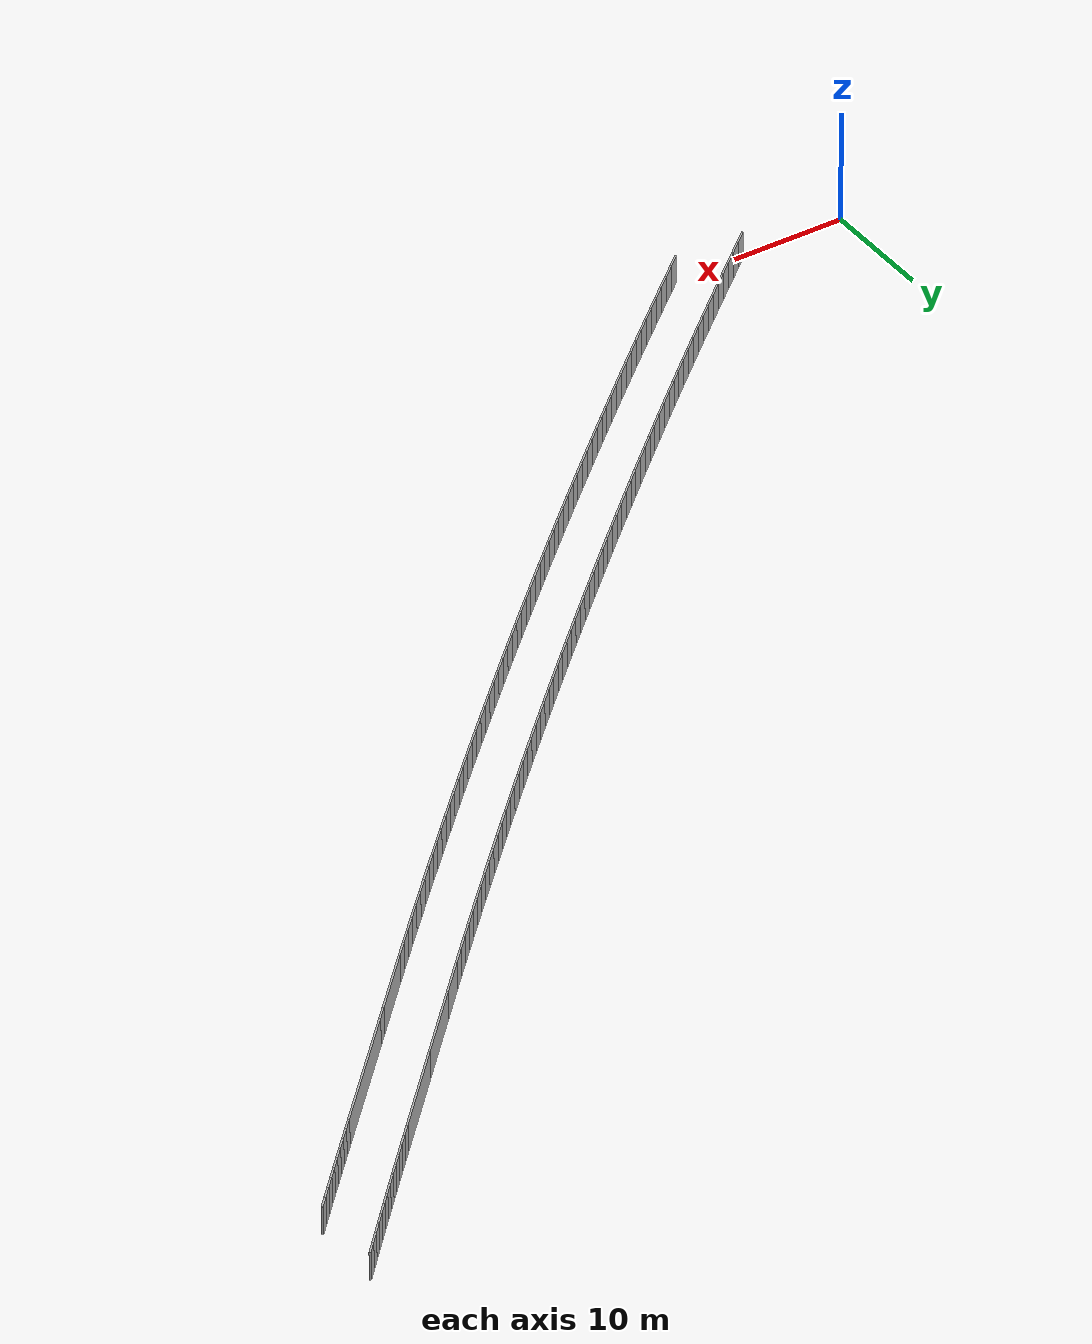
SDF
<?xml version="1.0" ?>
<sdf version="1.6">
  <model name="sps_1904">
    <pose frame="">0 0 0 0 -0 0</pose>
    <static>1</static>
    <self_collide>0</self_collide>
    <allow_auto_disable>0</allow_auto_disable>
    <link name="Wall243">
      <kinematic>0</kinematic>
      <gravity>1</gravity>
      <self_collide>0</self_collide>
      <collision name="collision">
        <geometry>
          <box>
            <size>8.3183 0.15 2.5</size>
          </box>
        </geometry>
        <pose frame="">0 0 0 0 -0 0</pose>
      </collision>
      <visual name="visual">
        <geometry>
          <box>
            <size>8.3183 0.15 2.5</size>
          </box>
        </geometry>
        <pose frame="">0 0 0 0 -0 0</pose>
        <cast_shadows>1</cast_shadows>
        <transparency>0.0</transparency>
      </visual>
      <pose frame="">87.3127 76.0104 1.25 0 0 -2.32351</pose>
    </link>
    <link name="Wall244">
      <kinematic>0</kinematic>
      <gravity>1</gravity>
      <self_collide>0</self_collide>
      <collision name="collision">
        <geometry>
          <box>
            <size>6.96301 0.15 2.5</size>
          </box>
        </geometry>
        <pose frame="">0 0 0 0 -0 0</pose>
      </collision>
      <visual name="visual">
        <geometry>
          <box>
            <size>6.96301 0.15 2.5</size>
          </box>
        </geometry>
        <pose frame="">0 0 0 0 -0 0</pose>
        <cast_shadows>1</cast_shadows>
        <transparency>0.0</transparency>
      </visual>
      <pose frame="">82.0894 70.434 1.25 0 0 -2.32351</pose>
    </link>
    <link name="Wall245">
      <kinematic>0</kinematic>
      <gravity>1</gravity>
      <self_collide>0</self_collide>
      <collision name="collision">
        <geometry>
          <box>
            <size>3.39064 0.15 2.5</size>
          </box>
        </geometry>
        <pose frame="">0 0 0 0 -0 0</pose>
      </collision>
      <visual name="visual">
        <geometry>
          <box>
            <size>3.39064 0.15 2.5</size>
          </box>
        </geometry>
        <pose frame="">0 0 0 0 -0 0</pose>
        <cast_shadows>1</cast_shadows>
        <transparency>0.0</transparency>
      </visual>
      <pose frame="">78.5504 66.6558 1.25 0 0 -2.32351</pose>
    </link>
    <link name="Wall309">
      <kinematic>0</kinematic>
      <gravity>1</gravity>
      <self_collide>0</self_collide>
      <collision name="collision">
        <geometry>
          <box>
            <size>5.94722 0.15 2.5</size>
          </box>
        </geometry>
        <pose frame="">0 0 0 0 -0 0</pose>
      </collision>
      <visual name="visual">
        <geometry>
          <box>
            <size>5.94722 0.15 2.5</size>
          </box>
        </geometry>
        <pose frame="">0 0 0 0 -0 0</pose>
        <cast_shadows>1</cast_shadows>
        <transparency>0.0</transparency>
      </visual>
      <pose frame="">82.4366 64.7482 1.25 0 -0 0.818091</pose>
    </link>
    <link name="Wall310">
      <kinematic>0</kinematic>
      <gravity>1</gravity>
      <self_collide>0</self_collide>
      <collision name="collision">
        <geometry>
          <box>
            <size>1.33544 0.15 2.5</size>
          </box>
        </geometry>
        <pose frame="">0 0 0 0 -0 0</pose>
      </collision>
      <visual name="visual">
        <geometry>
          <box>
            <size>1.33544 0.15 2.5</size>
          </box>
        </geometry>
        <pose frame="">0 0 0 0 -0 0</pose>
        <cast_shadows>1</cast_shadows>
        <transparency>0.0</transparency>
      </visual>
      <pose frame="">84.9259 67.4058 1.25 0 -0 0.818091</pose>
    </link>
    <link name="Wall311">
      <kinematic>0</kinematic>
      <gravity>1</gravity>
      <self_collide>0</self_collide>
      <collision name="collision">
        <geometry>
          <box>
            <size>11.3992 0.15 2.5</size>
          </box>
        </geometry>
        <pose frame="">0 0 0 0 -0 0</pose>
      </collision>
      <visual name="visual">
        <geometry>
          <box>
            <size>11.3992 0.15 2.5</size>
          </box>
        </geometry>
        <pose frame="">0 0 0 0 -0 0</pose>
        <cast_shadows>1</cast_shadows>
        <transparency>0.0</transparency>
      </visual>
      <pose frame="">89.2787 72.0529 1.25 0 -0 0.818091</pose>
    </link>
    <link name="Wall3417">
      <kinematic>0</kinematic>
      <gravity>1</gravity>
      <self_collide>0</self_collide>
      <collision name="collision">
        <geometry>
          <box>
            <size>1.07595 0.15 2.5</size>
          </box>
        </geometry>
        <pose frame="">0 0 0 0 -0 0</pose>
      </collision>
      <visual name="visual">
        <geometry>
          <box>
            <size>1.07595 0.15 2.5</size>
          </box>
        </geometry>
        <pose frame="">0 0 0 0 -0 0</pose>
        <cast_shadows>1</cast_shadows>
        <transparency>0.0</transparency>
      </visual>
      <pose frame="">90.5239 79.4385 1.25 0 -0 0.817935</pose>
    </link>
    <link name="Wall3418">
      <kinematic>0</kinematic>
      <gravity>1</gravity>
      <self_collide>0</self_collide>
      <collision name="collision">
        <geometry>
          <box>
            <size>1.07582 0.15 2.5</size>
          </box>
        </geometry>
        <pose frame="">0 0 0 0 -0 0</pose>
      </collision>
      <visual name="visual">
        <geometry>
          <box>
            <size>1.07582 0.15 2.5</size>
          </box>
        </geometry>
        <pose frame="">0 0 0 0 -0 0</pose>
        <cast_shadows>1</cast_shadows>
        <transparency>0.0</transparency>
      </visual>
      <pose frame="">91.259 80.2241 1.25 0 -0 0.819223</pose>
    </link>
    <link name="Wall3419">
      <kinematic>0</kinematic>
      <gravity>1</gravity>
      <self_collide>0</self_collide>
      <collision name="collision">
        <geometry>
          <box>
            <size>1.07616 0.15 2.5</size>
          </box>
        </geometry>
        <pose frame="">0 0 0 0 -0 0</pose>
      </collision>
      <visual name="visual">
        <geometry>
          <box>
            <size>1.07616 0.15 2.5</size>
          </box>
        </geometry>
        <pose frame="">0 0 0 0 -0 0</pose>
        <cast_shadows>1</cast_shadows>
        <transparency>0.0</transparency>
      </visual>
      <pose frame="">91.9932 81.0106 1.25 0 -0 0.820216</pose>
    </link>
    <link name="Wall3420">
      <kinematic>0</kinematic>
      <gravity>1</gravity>
      <self_collide>0</self_collide>
      <collision name="collision">
        <geometry>
          <box>
            <size>1.07594 0.15 2.5</size>
          </box>
        </geometry>
        <pose frame="">0 0 0 0 -0 0</pose>
      </collision>
      <visual name="visual">
        <geometry>
          <box>
            <size>1.07594 0.15 2.5</size>
          </box>
        </geometry>
        <pose frame="">0 0 0 0 -0 0</pose>
        <cast_shadows>1</cast_shadows>
        <transparency>0.0</transparency>
      </visual>
      <pose frame="">92.7268 81.7979 1.25 0 -0 0.821266</pose>
    </link>
    <link name="Wall3421">
      <kinematic>0</kinematic>
      <gravity>1</gravity>
      <self_collide>0</self_collide>
      <collision name="collision">
        <geometry>
          <box>
            <size>1.07598 0.15 2.5</size>
          </box>
        </geometry>
        <pose frame="">0 0 0 0 -0 0</pose>
      </collision>
      <visual name="visual">
        <geometry>
          <box>
            <size>1.07598 0.15 2.5</size>
          </box>
        </geometry>
        <pose frame="">0 0 0 0 -0 0</pose>
        <cast_shadows>1</cast_shadows>
        <transparency>0.0</transparency>
      </visual>
      <pose frame="">93.4594 82.5859 1.25 0 -0 0.822389</pose>
    </link>
    <link name="Wall3422">
      <kinematic>0</kinematic>
      <gravity>1</gravity>
      <self_collide>0</self_collide>
      <collision name="collision">
        <geometry>
          <box>
            <size>1.07599 0.15 2.5</size>
          </box>
        </geometry>
        <pose frame="">0 0 0 0 -0 0</pose>
      </collision>
      <visual name="visual">
        <geometry>
          <box>
            <size>1.07599 0.15 2.5</size>
          </box>
        </geometry>
        <pose frame="">0 0 0 0 -0 0</pose>
        <cast_shadows>1</cast_shadows>
        <transparency>0.0</transparency>
      </visual>
      <pose frame="">94.1911 83.3748 1.25 0 -0 0.823633</pose>
    </link>
    <link name="Wall3423">
      <kinematic>0</kinematic>
      <gravity>1</gravity>
      <self_collide>0</self_collide>
      <collision name="collision">
        <geometry>
          <box>
            <size>1.07608 0.15 2.5</size>
          </box>
        </geometry>
        <pose frame="">0 0 0 0 -0 0</pose>
      </collision>
      <visual name="visual">
        <geometry>
          <box>
            <size>1.07608 0.15 2.5</size>
          </box>
        </geometry>
        <pose frame="">0 0 0 0 -0 0</pose>
        <cast_shadows>1</cast_shadows>
        <transparency>0.0</transparency>
      </visual>
      <pose frame="">94.9219 84.1646 1.25 0 -0 0.824713</pose>
    </link>
    <link name="Wall3424">
      <kinematic>0</kinematic>
      <gravity>1</gravity>
      <self_collide>0</self_collide>
      <collision name="collision">
        <geometry>
          <box>
            <size>1.07596 0.15 2.5</size>
          </box>
        </geometry>
        <pose frame="">0 0 0 0 -0 0</pose>
      </collision>
      <visual name="visual">
        <geometry>
          <box>
            <size>1.07596 0.15 2.5</size>
          </box>
        </geometry>
        <pose frame="">0 0 0 0 -0 0</pose>
        <cast_shadows>1</cast_shadows>
        <transparency>0.0</transparency>
      </visual>
      <pose frame="">95.6518 84.9552 1.25 0 -0 0.825922</pose>
    </link>
    <link name="Wall3425">
      <kinematic>0</kinematic>
      <gravity>1</gravity>
      <self_collide>0</self_collide>
      <collision name="collision">
        <geometry>
          <box>
            <size>1.07584 0.15 2.5</size>
          </box>
        </geometry>
        <pose frame="">0 0 0 0 -0 0</pose>
      </collision>
      <visual name="visual">
        <geometry>
          <box>
            <size>1.07584 0.15 2.5</size>
          </box>
        </geometry>
        <pose frame="">0 0 0 0 -0 0</pose>
        <cast_shadows>1</cast_shadows>
        <transparency>0.0</transparency>
      </visual>
      <pose frame="">96.3806 85.7466 1.25 0 -0 0.827051</pose>
    </link>
    <link name="Wall3426">
      <kinematic>0</kinematic>
      <gravity>1</gravity>
      <self_collide>0</self_collide>
      <collision name="collision">
        <geometry>
          <box>
            <size>1.07609 0.15 2.5</size>
          </box>
        </geometry>
        <pose frame="">0 0 0 0 -0 0</pose>
      </collision>
      <visual name="visual">
        <geometry>
          <box>
            <size>1.07609 0.15 2.5</size>
          </box>
        </geometry>
        <pose frame="">0 0 0 0 -0 0</pose>
        <cast_shadows>1</cast_shadows>
        <transparency>0.0</transparency>
      </visual>
      <pose frame="">97.1088 86.5388 1.25 0 -0 0.827964</pose>
    </link>
    <link name="Wall3427">
      <kinematic>0</kinematic>
      <gravity>1</gravity>
      <self_collide>0</self_collide>
      <collision name="collision">
        <geometry>
          <box>
            <size>1.07616 0.15 2.5</size>
          </box>
        </geometry>
        <pose frame="">0 0 0 0 -0 0</pose>
      </collision>
      <visual name="visual">
        <geometry>
          <box>
            <size>1.07616 0.15 2.5</size>
          </box>
        </geometry>
        <pose frame="">0 0 0 0 -0 0</pose>
        <cast_shadows>1</cast_shadows>
        <transparency>0.0</transparency>
      </visual>
      <pose frame="">97.8361 87.3319 1.25 0 -0 0.829326</pose>
    </link>
    <link name="Wall3428">
      <kinematic>0</kinematic>
      <gravity>1</gravity>
      <self_collide>0</self_collide>
      <collision name="collision">
        <geometry>
          <box>
            <size>1.07586 0.15 2.5</size>
          </box>
        </geometry>
        <pose frame="">0 0 0 0 -0 0</pose>
      </collision>
      <visual name="visual">
        <geometry>
          <box>
            <size>1.07586 0.15 2.5</size>
          </box>
        </geometry>
        <pose frame="">0 0 0 0 -0 0</pose>
        <cast_shadows>1</cast_shadows>
        <transparency>0.0</transparency>
      </visual>
      <pose frame="">98.5624 88.1258 1.25 0 -0 0.830382</pose>
    </link>
    <link name="Wall3429">
      <kinematic>0</kinematic>
      <gravity>1</gravity>
      <self_collide>0</self_collide>
      <collision name="collision">
        <geometry>
          <box>
            <size>1.07605 0.15 2.5</size>
          </box>
        </geometry>
        <pose frame="">0 0 0 0 -0 0</pose>
      </collision>
      <visual name="visual">
        <geometry>
          <box>
            <size>1.07605 0.15 2.5</size>
          </box>
        </geometry>
        <pose frame="">0 0 0 0 -0 0</pose>
        <cast_shadows>1</cast_shadows>
        <transparency>0.0</transparency>
      </visual>
      <pose frame="">99.2877 88.9205 1.25 0 -0 0.831539</pose>
    </link>
    <link name="Wall4156">
      <kinematic>0</kinematic>
      <gravity>1</gravity>
      <self_collide>0</self_collide>
      <collision name="collision">
        <geometry>
          <box>
            <size>1.49647 0.15 2.5</size>
          </box>
        </geometry>
        <pose frame="">0 0 0 0 -0 0</pose>
      </collision>
      <visual name="visual">
        <geometry>
          <box>
            <size>1.49647 0.15 2.5</size>
          </box>
        </geometry>
        <pose frame="">0 0 0 0 -0 0</pose>
        <cast_shadows>1</cast_shadows>
        <transparency>0.0</transparency>
      </visual>
      <pose frame="">9.94445 0.671279 1.25 0 -0 0.715404</pose>
    </link>
    <link name="Wall4157">
      <kinematic>0</kinematic>
      <gravity>1</gravity>
      <self_collide>0</self_collide>
      <collision name="collision">
        <geometry>
          <box>
            <size>1.49663 0.15 2.5</size>
          </box>
        </geometry>
        <pose frame="">0 0 0 0 -0 0</pose>
      </collision>
      <visual name="visual">
        <geometry>
          <box>
            <size>1.49663 0.15 2.5</size>
          </box>
        </geometry>
        <pose frame="">0 0 0 0 -0 0</pose>
        <cast_shadows>1</cast_shadows>
        <transparency>0.0</transparency>
      </visual>
      <pose frame="">11.0732 1.65388 1.25 0 -0 0.717146</pose>
    </link>
    <link name="Wall4158">
      <kinematic>0</kinematic>
      <gravity>1</gravity>
      <self_collide>0</self_collide>
      <collision name="collision">
        <geometry>
          <box>
            <size>1.49644 0.15 2.5</size>
          </box>
        </geometry>
        <pose frame="">0 0 0 0 -0 0</pose>
      </collision>
      <visual name="visual">
        <geometry>
          <box>
            <size>1.49644 0.15 2.5</size>
          </box>
        </geometry>
        <pose frame="">0 0 0 0 -0 0</pose>
        <cast_shadows>1</cast_shadows>
        <transparency>0.0</transparency>
      </visual>
      <pose frame="">12.2004 2.63829 1.25 0 -0 0.718611</pose>
    </link>
    <link name="Wall4159">
      <kinematic>0</kinematic>
      <gravity>1</gravity>
      <self_collide>0</self_collide>
      <collision name="collision">
        <geometry>
          <box>
            <size>1.49675 0.15 2.5</size>
          </box>
        </geometry>
        <pose frame="">0 0 0 0 -0 0</pose>
      </collision>
      <visual name="visual">
        <geometry>
          <box>
            <size>1.49675 0.15 2.5</size>
          </box>
        </geometry>
        <pose frame="">0 0 0 0 -0 0</pose>
        <cast_shadows>1</cast_shadows>
        <transparency>0.0</transparency>
      </visual>
      <pose frame="">13.3261 3.6245 1.25 0 -0 0.720272</pose>
    </link>
    <link name="Wall4160">
      <kinematic>0</kinematic>
      <gravity>1</gravity>
      <self_collide>0</self_collide>
      <collision name="collision">
        <geometry>
          <box>
            <size>1.49643 0.15 2.5</size>
          </box>
        </geometry>
        <pose frame="">0 0 0 0 -0 0</pose>
      </collision>
      <visual name="visual">
        <geometry>
          <box>
            <size>1.49643 0.15 2.5</size>
          </box>
        </geometry>
        <pose frame="">0 0 0 0 -0 0</pose>
        <cast_shadows>1</cast_shadows>
        <transparency>0.0</transparency>
      </visual>
      <pose frame="">14.4502 4.6125 1.25 0 -0 0.721819</pose>
    </link>
    <link name="Wall4161">
      <kinematic>0</kinematic>
      <gravity>1</gravity>
      <self_collide>0</self_collide>
      <collision name="collision">
        <geometry>
          <box>
            <size>1.49654 0.15 2.5</size>
          </box>
        </geometry>
        <pose frame="">0 0 0 0 -0 0</pose>
      </collision>
      <visual name="visual">
        <geometry>
          <box>
            <size>1.49654 0.15 2.5</size>
          </box>
        </geometry>
        <pose frame="">0 0 0 0 -0 0</pose>
        <cast_shadows>1</cast_shadows>
        <transparency>0.0</transparency>
      </visual>
      <pose frame="">15.5727 5.60219 1.25 0 -0 0.723384</pose>
    </link>
    <link name="Wall4162">
      <kinematic>0</kinematic>
      <gravity>1</gravity>
      <self_collide>0</self_collide>
      <collision name="collision">
        <geometry>
          <box>
            <size>1.49645 0.15 2.5</size>
          </box>
        </geometry>
        <pose frame="">0 0 0 0 -0 0</pose>
      </collision>
      <visual name="visual">
        <geometry>
          <box>
            <size>1.49645 0.15 2.5</size>
          </box>
        </geometry>
        <pose frame="">0 0 0 0 -0 0</pose>
        <cast_shadows>1</cast_shadows>
        <transparency>0.0</transparency>
      </visual>
      <pose frame="">16.6937 6.59358 1.25 0 -0 0.724854</pose>
    </link>
    <link name="Wall4163">
      <kinematic>0</kinematic>
      <gravity>1</gravity>
      <self_collide>0</self_collide>
      <collision name="collision">
        <geometry>
          <box>
            <size>1.49642 0.15 2.5</size>
          </box>
        </geometry>
        <pose frame="">0 0 0 0 -0 0</pose>
      </collision>
      <visual name="visual">
        <geometry>
          <box>
            <size>1.49642 0.15 2.5</size>
          </box>
        </geometry>
        <pose frame="">0 0 0 0 -0 0</pose>
        <cast_shadows>1</cast_shadows>
        <transparency>0.0</transparency>
      </visual>
      <pose frame="">17.8131 7.58678 1.25 0 -0 0.726673</pose>
    </link>
    <link name="Wall4164">
      <kinematic>0</kinematic>
      <gravity>1</gravity>
      <self_collide>0</self_collide>
      <collision name="collision">
        <geometry>
          <box>
            <size>1.49643 0.15 2.5</size>
          </box>
        </geometry>
        <pose frame="">0 0 0 0 -0 0</pose>
      </collision>
      <visual name="visual">
        <geometry>
          <box>
            <size>1.49643 0.15 2.5</size>
          </box>
        </geometry>
        <pose frame="">0 0 0 0 -0 0</pose>
        <cast_shadows>1</cast_shadows>
        <transparency>0.0</transparency>
      </visual>
      <pose frame="">18.9308 8.58177 1.25 0 -0 0.728089</pose>
    </link>
    <link name="Wall4165">
      <kinematic>0</kinematic>
      <gravity>1</gravity>
      <self_collide>0</self_collide>
      <collision name="collision">
        <geometry>
          <box>
            <size>1.49672 0.15 2.5</size>
          </box>
        </geometry>
        <pose frame="">0 0 0 0 -0 0</pose>
      </collision>
      <visual name="visual">
        <geometry>
          <box>
            <size>1.49672 0.15 2.5</size>
          </box>
        </geometry>
        <pose frame="">0 0 0 0 -0 0</pose>
        <cast_shadows>1</cast_shadows>
        <transparency>0.0</transparency>
      </visual>
      <pose frame="">20.0471 9.57857 1.25 0 -0 0.729717</pose>
    </link>
    <link name="Wall4166">
      <kinematic>0</kinematic>
      <gravity>1</gravity>
      <self_collide>0</self_collide>
      <collision name="collision">
        <geometry>
          <box>
            <size>1.49646 0.15 2.5</size>
          </box>
        </geometry>
        <pose frame="">0 0 0 0 -0 0</pose>
      </collision>
      <visual name="visual">
        <geometry>
          <box>
            <size>1.49646 0.15 2.5</size>
          </box>
        </geometry>
        <pose frame="">0 0 0 0 -0 0</pose>
        <cast_shadows>1</cast_shadows>
        <transparency>0.0</transparency>
      </visual>
      <pose frame="">21.1618 10.5772 1.25 0 -0 0.731354</pose>
    </link>
    <link name="Wall4167">
      <kinematic>0</kinematic>
      <gravity>1</gravity>
      <self_collide>0</self_collide>
      <collision name="collision">
        <geometry>
          <box>
            <size>1.49642 0.15 2.5</size>
          </box>
        </geometry>
        <pose frame="">0 0 0 0 -0 0</pose>
      </collision>
      <visual name="visual">
        <geometry>
          <box>
            <size>1.49642 0.15 2.5</size>
          </box>
        </geometry>
        <pose frame="">0 0 0 0 -0 0</pose>
        <cast_shadows>1</cast_shadows>
        <transparency>0.0</transparency>
      </visual>
      <pose frame="">22.2747 11.5775 1.25 0 -0 0.732912</pose>
    </link>
    <link name="Wall4168">
      <kinematic>0</kinematic>
      <gravity>1</gravity>
      <self_collide>0</self_collide>
      <collision name="collision">
        <geometry>
          <box>
            <size>1.49665 0.15 2.5</size>
          </box>
        </geometry>
        <pose frame="">0 0 0 0 -0 0</pose>
      </collision>
      <visual name="visual">
        <geometry>
          <box>
            <size>1.49665 0.15 2.5</size>
          </box>
        </geometry>
        <pose frame="">0 0 0 0 -0 0</pose>
        <cast_shadows>1</cast_shadows>
        <transparency>0.0</transparency>
      </visual>
      <pose frame="">23.3863 12.5796 1.25 0 -0 0.734422</pose>
    </link>
    <link name="Wall4169">
      <kinematic>0</kinematic>
      <gravity>1</gravity>
      <self_collide>0</self_collide>
      <collision name="collision">
        <geometry>
          <box>
            <size>1.49665 0.15 2.5</size>
          </box>
        </geometry>
        <pose frame="">0 0 0 0 -0 0</pose>
      </collision>
      <visual name="visual">
        <geometry>
          <box>
            <size>1.49665 0.15 2.5</size>
          </box>
        </geometry>
        <pose frame="">0 0 0 0 -0 0</pose>
        <cast_shadows>1</cast_shadows>
        <transparency>0.0</transparency>
      </visual>
      <pose frame="">24.4963 13.5835 1.25 0 -0 0.736068</pose>
    </link>
    <link name="Wall4170">
      <kinematic>0</kinematic>
      <gravity>1</gravity>
      <self_collide>0</self_collide>
      <collision name="collision">
        <geometry>
          <box>
            <size>1.49649 0.15 2.5</size>
          </box>
        </geometry>
        <pose frame="">0 0 0 0 -0 0</pose>
      </collision>
      <visual name="visual">
        <geometry>
          <box>
            <size>1.49649 0.15 2.5</size>
          </box>
        </geometry>
        <pose frame="">0 0 0 0 -0 0</pose>
        <cast_shadows>1</cast_shadows>
        <transparency>0.0</transparency>
      </visual>
      <pose frame="">25.6045 14.5892 1.25 0 -0 0.737766</pose>
    </link>
    <link name="Wall4171">
      <kinematic>0</kinematic>
      <gravity>1</gravity>
      <self_collide>0</self_collide>
      <collision name="collision">
        <geometry>
          <box>
            <size>1.4966 0.15 2.5</size>
          </box>
        </geometry>
        <pose frame="">0 0 0 0 -0 0</pose>
      </collision>
      <visual name="visual">
        <geometry>
          <box>
            <size>1.4966 0.15 2.5</size>
          </box>
        </geometry>
        <pose frame="">0 0 0 0 -0 0</pose>
        <cast_shadows>1</cast_shadows>
        <transparency>0.0</transparency>
      </visual>
      <pose frame="">26.7112 15.5966 1.25 0 -0 0.739184</pose>
    </link>
    <link name="Wall4172">
      <kinematic>0</kinematic>
      <gravity>1</gravity>
      <self_collide>0</self_collide>
      <collision name="collision">
        <geometry>
          <box>
            <size>1.4964 0.15 2.5</size>
          </box>
        </geometry>
        <pose frame="">0 0 0 0 -0 0</pose>
      </collision>
      <visual name="visual">
        <geometry>
          <box>
            <size>1.4964 0.15 2.5</size>
          </box>
        </geometry>
        <pose frame="">0 0 0 0 -0 0</pose>
        <cast_shadows>1</cast_shadows>
        <transparency>0.0</transparency>
      </visual>
      <pose frame="">27.8163 16.6057 1.25 0 -0 0.740852</pose>
    </link>
    <link name="Wall4173">
      <kinematic>0</kinematic>
      <gravity>1</gravity>
      <self_collide>0</self_collide>
      <collision name="collision">
        <geometry>
          <box>
            <size>1.49669 0.15 2.5</size>
          </box>
        </geometry>
        <pose frame="">0 0 0 0 -0 0</pose>
      </collision>
      <visual name="visual">
        <geometry>
          <box>
            <size>1.49669 0.15 2.5</size>
          </box>
        </geometry>
        <pose frame="">0 0 0 0 -0 0</pose>
        <cast_shadows>1</cast_shadows>
        <transparency>0.0</transparency>
      </visual>
      <pose frame="">28.9199 17.6166 1.25 0 -0 0.742391</pose>
    </link>
    <link name="Wall4174">
      <kinematic>0</kinematic>
      <gravity>1</gravity>
      <self_collide>0</self_collide>
      <collision name="collision">
        <geometry>
          <box>
            <size>1.49651 0.15 2.5</size>
          </box>
        </geometry>
        <pose frame="">0 0 0 0 -0 0</pose>
      </collision>
      <visual name="visual">
        <geometry>
          <box>
            <size>1.49651 0.15 2.5</size>
          </box>
        </geometry>
        <pose frame="">0 0 0 0 -0 0</pose>
        <cast_shadows>1</cast_shadows>
        <transparency>0.0</transparency>
      </visual>
      <pose frame="">30.0219 18.6292 1.25 0 -0 0.743886</pose>
    </link>
    <link name="Wall4175">
      <kinematic>0</kinematic>
      <gravity>1</gravity>
      <self_collide>0</self_collide>
      <collision name="collision">
        <geometry>
          <box>
            <size>1.49641 0.15 2.5</size>
          </box>
        </geometry>
        <pose frame="">0 0 0 0 -0 0</pose>
      </collision>
      <visual name="visual">
        <geometry>
          <box>
            <size>1.49641 0.15 2.5</size>
          </box>
        </geometry>
        <pose frame="">0 0 0 0 -0 0</pose>
        <cast_shadows>1</cast_shadows>
        <transparency>0.0</transparency>
      </visual>
      <pose frame="">31.1222 19.6435 1.25 0 -0 0.745615</pose>
    </link>
    <link name="Wall4176">
      <kinematic>0</kinematic>
      <gravity>1</gravity>
      <self_collide>0</self_collide>
      <collision name="collision">
        <geometry>
          <box>
            <size>1.49666 0.15 2.5</size>
          </box>
        </geometry>
        <pose frame="">0 0 0 0 -0 0</pose>
      </collision>
      <visual name="visual">
        <geometry>
          <box>
            <size>1.49666 0.15 2.5</size>
          </box>
        </geometry>
        <pose frame="">0 0 0 0 -0 0</pose>
        <cast_shadows>1</cast_shadows>
        <transparency>0.0</transparency>
      </visual>
      <pose frame="">32.2208 20.6596 1.25 0 -0 0.747123</pose>
    </link>
    <link name="Wall4177">
      <kinematic>0</kinematic>
      <gravity>1</gravity>
      <self_collide>0</self_collide>
      <collision name="collision">
        <geometry>
          <box>
            <size>1.49652 0.15 2.5</size>
          </box>
        </geometry>
        <pose frame="">0 0 0 0 -0 0</pose>
      </collision>
      <visual name="visual">
        <geometry>
          <box>
            <size>1.49652 0.15 2.5</size>
          </box>
        </geometry>
        <pose frame="">0 0 0 0 -0 0</pose>
        <cast_shadows>1</cast_shadows>
        <transparency>0.0</transparency>
      </visual>
      <pose frame="">33.318 21.6775 1.25 0 -0 0.748822</pose>
    </link>
    <link name="Wall4178">
      <kinematic>0</kinematic>
      <gravity>1</gravity>
      <self_collide>0</self_collide>
      <collision name="collision">
        <geometry>
          <box>
            <size>1.49657 0.15 2.5</size>
          </box>
        </geometry>
        <pose frame="">0 0 0 0 -0 0</pose>
      </collision>
      <visual name="visual">
        <geometry>
          <box>
            <size>1.49657 0.15 2.5</size>
          </box>
        </geometry>
        <pose frame="">0 0 0 0 -0 0</pose>
        <cast_shadows>1</cast_shadows>
        <transparency>0.0</transparency>
      </visual>
      <pose frame="">34.4134 22.6972 1.25 0 -0 0.75041</pose>
    </link>
    <link name="Wall4179">
      <kinematic>0</kinematic>
      <gravity>1</gravity>
      <self_collide>0</self_collide>
      <collision name="collision">
        <geometry>
          <box>
            <size>1.49653 0.15 2.5</size>
          </box>
        </geometry>
        <pose frame="">0 0 0 0 -0 0</pose>
      </collision>
      <visual name="visual">
        <geometry>
          <box>
            <size>1.49653 0.15 2.5</size>
          </box>
        </geometry>
        <pose frame="">0 0 0 0 -0 0</pose>
        <cast_shadows>1</cast_shadows>
        <transparency>0.0</transparency>
      </visual>
      <pose frame="">35.5072 23.7186 1.25 0 -0 0.751939</pose>
    </link>
    <link name="Wall4180">
      <kinematic>0</kinematic>
      <gravity>1</gravity>
      <self_collide>0</self_collide>
      <collision name="collision">
        <geometry>
          <box>
            <size>1.49642 0.15 2.5</size>
          </box>
        </geometry>
        <pose frame="">0 0 0 0 -0 0</pose>
      </collision>
      <visual name="visual">
        <geometry>
          <box>
            <size>1.49642 0.15 2.5</size>
          </box>
        </geometry>
        <pose frame="">0 0 0 0 -0 0</pose>
        <cast_shadows>1</cast_shadows>
        <transparency>0.0</transparency>
      </visual>
      <pose frame="">36.5994 24.7416 1.25 0 -0 0.753466</pose>
    </link>
    <link name="Wall4181">
      <kinematic>0</kinematic>
      <gravity>1</gravity>
      <self_collide>0</self_collide>
      <collision name="collision">
        <geometry>
          <box>
            <size>1.49665 0.15 2.5</size>
          </box>
        </geometry>
        <pose frame="">0 0 0 0 -0 0</pose>
      </collision>
      <visual name="visual">
        <geometry>
          <box>
            <size>1.49665 0.15 2.5</size>
          </box>
        </geometry>
        <pose frame="">0 0 0 0 -0 0</pose>
        <cast_shadows>1</cast_shadows>
        <transparency>0.0</transparency>
      </visual>
      <pose frame="">37.6901 25.7663 1.25 0 -0 0.754942</pose>
    </link>
    <link name="Wall4182">
      <kinematic>0</kinematic>
      <gravity>1</gravity>
      <self_collide>0</self_collide>
      <collision name="collision">
        <geometry>
          <box>
            <size>1.49645 0.15 2.5</size>
          </box>
        </geometry>
        <pose frame="">0 0 0 0 -0 0</pose>
      </collision>
      <visual name="visual">
        <geometry>
          <box>
            <size>1.49645 0.15 2.5</size>
          </box>
        </geometry>
        <pose frame="">0 0 0 0 -0 0</pose>
        <cast_shadows>1</cast_shadows>
        <transparency>0.0</transparency>
      </visual>
      <pose frame="">38.7792 26.7927 1.25 0 -0 0.756582</pose>
    </link>
    <link name="Wall4183">
      <kinematic>0</kinematic>
      <gravity>1</gravity>
      <self_collide>0</self_collide>
      <collision name="collision">
        <geometry>
          <box>
            <size>1.49633 0.15 2.5</size>
          </box>
        </geometry>
        <pose frame="">0 0 0 0 -0 0</pose>
      </collision>
      <visual name="visual">
        <geometry>
          <box>
            <size>1.49633 0.15 2.5</size>
          </box>
        </geometry>
        <pose frame="">0 0 0 0 -0 0</pose>
        <cast_shadows>1</cast_shadows>
        <transparency>0.0</transparency>
      </visual>
      <pose frame="">39.8664 27.8208 1.25 0 -0 0.758283</pose>
    </link>
    <link name="Wall4184">
      <kinematic>0</kinematic>
      <gravity>1</gravity>
      <self_collide>0</self_collide>
      <collision name="collision">
        <geometry>
          <box>
            <size>1.49675 0.15 2.5</size>
          </box>
        </geometry>
        <pose frame="">0 0 0 0 -0 0</pose>
      </collision>
      <visual name="visual">
        <geometry>
          <box>
            <size>1.49675 0.15 2.5</size>
          </box>
        </geometry>
        <pose frame="">0 0 0 0 -0 0</pose>
        <cast_shadows>1</cast_shadows>
        <transparency>0.0</transparency>
      </visual>
      <pose frame="">40.9521 28.8508 1.25 0 -0 0.759877</pose>
    </link>
    <link name="Wall4185">
      <kinematic>0</kinematic>
      <gravity>1</gravity>
      <self_collide>0</self_collide>
      <collision name="collision">
        <geometry>
          <box>
            <size>1.49651 0.15 2.5</size>
          </box>
        </geometry>
        <pose frame="">0 0 0 0 -0 0</pose>
      </collision>
      <visual name="visual">
        <geometry>
          <box>
            <size>1.49651 0.15 2.5</size>
          </box>
        </geometry>
        <pose frame="">0 0 0 0 -0 0</pose>
        <cast_shadows>1</cast_shadows>
        <transparency>0.0</transparency>
      </visual>
      <pose frame="">42.0362 29.8826 1.25 0 -0 0.761488</pose>
    </link>
    <link name="Wall4186">
      <kinematic>0</kinematic>
      <gravity>1</gravity>
      <self_collide>0</self_collide>
      <collision name="collision">
        <geometry>
          <box>
            <size>1.49633 0.15 2.5</size>
          </box>
        </geometry>
        <pose frame="">0 0 0 0 -0 0</pose>
      </collision>
      <visual name="visual">
        <geometry>
          <box>
            <size>1.49633 0.15 2.5</size>
          </box>
        </geometry>
        <pose frame="">0 0 0 0 -0 0</pose>
        <cast_shadows>1</cast_shadows>
        <transparency>0.0</transparency>
      </visual>
      <pose frame="">43.1186 30.9159 1.25 0 -0 0.762899</pose>
    </link>
    <link name="Wall4187">
      <kinematic>0</kinematic>
      <gravity>1</gravity>
      <self_collide>0</self_collide>
      <collision name="collision">
        <geometry>
          <box>
            <size>1.49658 0.15 2.5</size>
          </box>
        </geometry>
        <pose frame="">0 0 0 0 -0 0</pose>
      </collision>
      <visual name="visual">
        <geometry>
          <box>
            <size>1.49658 0.15 2.5</size>
          </box>
        </geometry>
        <pose frame="">0 0 0 0 -0 0</pose>
        <cast_shadows>1</cast_shadows>
        <transparency>0.0</transparency>
      </visual>
      <pose frame="">44.1995 31.9509 1.25 0 -0 0.764604</pose>
    </link>
    <link name="Wall4188">
      <kinematic>0</kinematic>
      <gravity>1</gravity>
      <self_collide>0</self_collide>
      <collision name="collision">
        <geometry>
          <box>
            <size>1.49662 0.15 2.5</size>
          </box>
        </geometry>
        <pose frame="">0 0 0 0 -0 0</pose>
      </collision>
      <visual name="visual">
        <geometry>
          <box>
            <size>1.49662 0.15 2.5</size>
          </box>
        </geometry>
        <pose frame="">0 0 0 0 -0 0</pose>
        <cast_shadows>1</cast_shadows>
        <transparency>0.0</transparency>
      </visual>
      <pose frame="">45.2786 32.9878 1.25 0 -0 0.76622</pose>
    </link>
    <link name="Wall4189">
      <kinematic>0</kinematic>
      <gravity>1</gravity>
      <self_collide>0</self_collide>
      <collision name="collision">
        <geometry>
          <box>
            <size>1.49649 0.15 2.5</size>
          </box>
        </geometry>
        <pose frame="">0 0 0 0 -0 0</pose>
      </collision>
      <visual name="visual">
        <geometry>
          <box>
            <size>1.49649 0.15 2.5</size>
          </box>
        </geometry>
        <pose frame="">0 0 0 0 -0 0</pose>
        <cast_shadows>1</cast_shadows>
        <transparency>0.0</transparency>
      </visual>
      <pose frame="">46.3561 34.0264 1.25 0 -0 0.767834</pose>
    </link>
    <link name="Wall4190">
      <kinematic>0</kinematic>
      <gravity>1</gravity>
      <self_collide>0</self_collide>
      <collision name="collision">
        <geometry>
          <box>
            <size>1.49645 0.15 2.5</size>
          </box>
        </geometry>
        <pose frame="">0 0 0 0 -0 0</pose>
      </collision>
      <visual name="visual">
        <geometry>
          <box>
            <size>1.49645 0.15 2.5</size>
          </box>
        </geometry>
        <pose frame="">0 0 0 0 -0 0</pose>
        <cast_shadows>1</cast_shadows>
        <transparency>0.0</transparency>
      </visual>
      <pose frame="">47.4319 35.0666 1.25 0 -0 0.769333</pose>
    </link>
    <link name="Wall4191">
      <kinematic>0</kinematic>
      <gravity>1</gravity>
      <self_collide>0</self_collide>
      <collision name="collision">
        <geometry>
          <box>
            <size>1.4968 0.15 2.5</size>
          </box>
        </geometry>
        <pose frame="">0 0 0 0 -0 0</pose>
      </collision>
      <visual name="visual">
        <geometry>
          <box>
            <size>1.4968 0.15 2.5</size>
          </box>
        </geometry>
        <pose frame="">0 0 0 0 -0 0</pose>
        <cast_shadows>1</cast_shadows>
        <transparency>0.0</transparency>
      </visual>
      <pose frame="">48.5062 36.1086 1.25 0 -0 0.770923</pose>
    </link>
    <link name="Wall4192">
      <kinematic>0</kinematic>
      <gravity>1</gravity>
      <self_collide>0</self_collide>
      <collision name="collision">
        <geometry>
          <box>
            <size>1.49651 0.15 2.5</size>
          </box>
        </geometry>
        <pose frame="">0 0 0 0 -0 0</pose>
      </collision>
      <visual name="visual">
        <geometry>
          <box>
            <size>1.49651 0.15 2.5</size>
          </box>
        </geometry>
        <pose frame="">0 0 0 0 -0 0</pose>
        <cast_shadows>1</cast_shadows>
        <transparency>0.0</transparency>
      </visual>
      <pose frame="">49.5789 37.1523 1.25 0 -0 0.772478</pose>
    </link>
    <link name="Wall4193">
      <kinematic>0</kinematic>
      <gravity>1</gravity>
      <self_collide>0</self_collide>
      <collision name="collision">
        <geometry>
          <box>
            <size>1.49631 0.15 2.5</size>
          </box>
        </geometry>
        <pose frame="">0 0 0 0 -0 0</pose>
      </collision>
      <visual name="visual">
        <geometry>
          <box>
            <size>1.49631 0.15 2.5</size>
          </box>
        </geometry>
        <pose frame="">0 0 0 0 -0 0</pose>
        <cast_shadows>1</cast_shadows>
        <transparency>0.0</transparency>
      </visual>
      <pose frame="">50.6498 38.1975 1.25 0 -0 0.774034</pose>
    </link>
    <link name="Wall4194">
      <kinematic>0</kinematic>
      <gravity>1</gravity>
      <self_collide>0</self_collide>
      <collision name="collision">
        <geometry>
          <box>
            <size>1.49659 0.15 2.5</size>
          </box>
        </geometry>
        <pose frame="">0 0 0 0 -0 0</pose>
      </collision>
      <visual name="visual">
        <geometry>
          <box>
            <size>1.49659 0.15 2.5</size>
          </box>
        </geometry>
        <pose frame="">0 0 0 0 -0 0</pose>
        <cast_shadows>1</cast_shadows>
        <transparency>0.0</transparency>
      </visual>
      <pose frame="">51.7191 39.2444 1.25 0 -0 0.775564</pose>
    </link>
    <link name="Wall4195">
      <kinematic>0</kinematic>
      <gravity>1</gravity>
      <self_collide>0</self_collide>
      <collision name="collision">
        <geometry>
          <box>
            <size>1.49656 0.15 2.5</size>
          </box>
        </geometry>
        <pose frame="">0 0 0 0 -0 0</pose>
      </collision>
      <visual name="visual">
        <geometry>
          <box>
            <size>1.49656 0.15 2.5</size>
          </box>
        </geometry>
        <pose frame="">0 0 0 0 -0 0</pose>
        <cast_shadows>1</cast_shadows>
        <transparency>0.0</transparency>
      </visual>
      <pose frame="">52.7867 40.2932 1.25 0 -0 0.777468</pose>
    </link>
    <link name="Wall4196">
      <kinematic>0</kinematic>
      <gravity>1</gravity>
      <self_collide>0</self_collide>
      <collision name="collision">
        <geometry>
          <box>
            <size>1.49659 0.15 2.5</size>
          </box>
        </geometry>
        <pose frame="">0 0 0 0 -0 0</pose>
      </collision>
      <visual name="visual">
        <geometry>
          <box>
            <size>1.49659 0.15 2.5</size>
          </box>
        </geometry>
        <pose frame="">0 0 0 0 -0 0</pose>
        <cast_shadows>1</cast_shadows>
        <transparency>0.0</transparency>
      </visual>
      <pose frame="">53.8527 41.3437 1.25 0 -0 0.778765</pose>
    </link>
    <link name="Wall4197">
      <kinematic>0</kinematic>
      <gravity>1</gravity>
      <self_collide>0</self_collide>
      <collision name="collision">
        <geometry>
          <box>
            <size>1.49653 0.15 2.5</size>
          </box>
        </geometry>
        <pose frame="">0 0 0 0 -0 0</pose>
      </collision>
      <visual name="visual">
        <geometry>
          <box>
            <size>1.49653 0.15 2.5</size>
          </box>
        </geometry>
        <pose frame="">0 0 0 0 -0 0</pose>
        <cast_shadows>1</cast_shadows>
        <transparency>0.0</transparency>
      </visual>
      <pose frame="">54.917 42.3958 1.25 0 -0 0.780524</pose>
    </link>
    <link name="Wall4198">
      <kinematic>0</kinematic>
      <gravity>1</gravity>
      <self_collide>0</self_collide>
      <collision name="collision">
        <geometry>
          <box>
            <size>1.49653 0.15 2.5</size>
          </box>
        </geometry>
        <pose frame="">0 0 0 0 -0 0</pose>
      </collision>
      <visual name="visual">
        <geometry>
          <box>
            <size>1.49653 0.15 2.5</size>
          </box>
        </geometry>
        <pose frame="">0 0 0 0 -0 0</pose>
        <cast_shadows>1</cast_shadows>
        <transparency>0.0</transparency>
      </visual>
      <pose frame="">55.9795 43.4496 1.25 0 -0 0.781966</pose>
    </link>
    <link name="Wall4199">
      <kinematic>0</kinematic>
      <gravity>1</gravity>
      <self_collide>0</self_collide>
      <collision name="collision">
        <geometry>
          <box>
            <size>1.49652 0.15 2.5</size>
          </box>
        </geometry>
        <pose frame="">0 0 0 0 -0 0</pose>
      </collision>
      <visual name="visual">
        <geometry>
          <box>
            <size>1.49652 0.15 2.5</size>
          </box>
        </geometry>
        <pose frame="">0 0 0 0 -0 0</pose>
        <cast_shadows>1</cast_shadows>
        <transparency>0.0</transparency>
      </visual>
      <pose frame="">57.0405 44.505 1.25 0 -0 0.783524</pose>
    </link>
    <link name="Wall4200">
      <kinematic>0</kinematic>
      <gravity>1</gravity>
      <self_collide>0</self_collide>
      <collision name="collision">
        <geometry>
          <box>
            <size>1.49665 0.15 2.5</size>
          </box>
        </geometry>
        <pose frame="">0 0 0 0 -0 0</pose>
      </collision>
      <visual name="visual">
        <geometry>
          <box>
            <size>1.49665 0.15 2.5</size>
          </box>
        </geometry>
        <pose frame="">0 0 0 0 -0 0</pose>
        <cast_shadows>1</cast_shadows>
        <transparency>0.0</transparency>
      </visual>
      <pose frame="">58.0999 45.5621 1.25 0 -0 0.78511</pose>
    </link>
    <link name="Wall4201">
      <kinematic>0</kinematic>
      <gravity>1</gravity>
      <self_collide>0</self_collide>
      <collision name="collision">
        <geometry>
          <box>
            <size>1.49643 0.15 2.5</size>
          </box>
        </geometry>
        <pose frame="">0 0 0 0 -0 0</pose>
      </collision>
      <visual name="visual">
        <geometry>
          <box>
            <size>1.49643 0.15 2.5</size>
          </box>
        </geometry>
        <pose frame="">0 0 0 0 -0 0</pose>
        <cast_shadows>1</cast_shadows>
        <transparency>0.0</transparency>
      </visual>
      <pose frame="">59.1576 46.6209 1.25 0 -0 0.786811</pose>
    </link>
    <link name="Wall4202">
      <kinematic>0</kinematic>
      <gravity>1</gravity>
      <self_collide>0</self_collide>
      <collision name="collision">
        <geometry>
          <box>
            <size>1.49652 0.15 2.5</size>
          </box>
        </geometry>
        <pose frame="">0 0 0 0 -0 0</pose>
      </collision>
      <visual name="visual">
        <geometry>
          <box>
            <size>1.49652 0.15 2.5</size>
          </box>
        </geometry>
        <pose frame="">0 0 0 0 -0 0</pose>
        <cast_shadows>1</cast_shadows>
        <transparency>0.0</transparency>
      </visual>
      <pose frame="">60.2134 47.6814 1.25 0 -0 0.788426</pose>
    </link>
    <link name="Wall4203">
      <kinematic>0</kinematic>
      <gravity>1</gravity>
      <self_collide>0</self_collide>
      <collision name="collision">
        <geometry>
          <box>
            <size>1.49653 0.15 2.5</size>
          </box>
        </geometry>
        <pose frame="">0 0 0 0 -0 0</pose>
      </collision>
      <visual name="visual">
        <geometry>
          <box>
            <size>1.49653 0.15 2.5</size>
          </box>
        </geometry>
        <pose frame="">0 0 0 0 -0 0</pose>
        <cast_shadows>1</cast_shadows>
        <transparency>0.0</transparency>
      </visual>
      <pose frame="">61.2676 48.7436 1.25 0 -0 0.789926</pose>
    </link>
    <link name="Wall4204">
      <kinematic>0</kinematic>
      <gravity>1</gravity>
      <self_collide>0</self_collide>
      <collision name="collision">
        <geometry>
          <box>
            <size>1.4965 0.15 2.5</size>
          </box>
        </geometry>
        <pose frame="">0 0 0 0 -0 0</pose>
      </collision>
      <visual name="visual">
        <geometry>
          <box>
            <size>1.4965 0.15 2.5</size>
          </box>
        </geometry>
        <pose frame="">0 0 0 0 -0 0</pose>
        <cast_shadows>1</cast_shadows>
        <transparency>0.0</transparency>
      </visual>
      <pose frame="">62.3202 49.8074 1.25 0 -0 0.791455</pose>
    </link>
    <link name="Wall4205">
      <kinematic>0</kinematic>
      <gravity>1</gravity>
      <self_collide>0</self_collide>
      <collision name="collision">
        <geometry>
          <box>
            <size>1.4966 0.15 2.5</size>
          </box>
        </geometry>
        <pose frame="">0 0 0 0 -0 0</pose>
      </collision>
      <visual name="visual">
        <geometry>
          <box>
            <size>1.4966 0.15 2.5</size>
          </box>
        </geometry>
        <pose frame="">0 0 0 0 -0 0</pose>
        <cast_shadows>1</cast_shadows>
        <transparency>0.0</transparency>
      </visual>
      <pose frame="">63.3711 50.8729 1.25 0 -0 0.793127</pose>
    </link>
    <link name="Wall4206">
      <kinematic>0</kinematic>
      <gravity>1</gravity>
      <self_collide>0</self_collide>
      <collision name="collision">
        <geometry>
          <box>
            <size>1.49641 0.15 2.5</size>
          </box>
        </geometry>
        <pose frame="">0 0 0 0 -0 0</pose>
      </collision>
      <visual name="visual">
        <geometry>
          <box>
            <size>1.49641 0.15 2.5</size>
          </box>
        </geometry>
        <pose frame="">0 0 0 0 -0 0</pose>
        <cast_shadows>1</cast_shadows>
        <transparency>0.0</transparency>
      </visual>
      <pose frame="">64.4202 51.9401 1.25 0 -0 0.794772</pose>
    </link>
    <link name="Wall4207">
      <kinematic>0</kinematic>
      <gravity>1</gravity>
      <self_collide>0</self_collide>
      <collision name="collision">
        <geometry>
          <box>
            <size>1.49665 0.15 2.5</size>
          </box>
        </geometry>
        <pose frame="">0 0 0 0 -0 0</pose>
      </collision>
      <visual name="visual">
        <geometry>
          <box>
            <size>1.49665 0.15 2.5</size>
          </box>
        </geometry>
        <pose frame="">0 0 0 0 -0 0</pose>
        <cast_shadows>1</cast_shadows>
        <transparency>0.0</transparency>
      </visual>
      <pose frame="">65.4676 53.0089 1.25 0 -0 0.796183</pose>
    </link>
    <link name="Wall4208">
      <kinematic>0</kinematic>
      <gravity>1</gravity>
      <self_collide>0</self_collide>
      <collision name="collision">
        <geometry>
          <box>
            <size>1.49646 0.15 2.5</size>
          </box>
        </geometry>
        <pose frame="">0 0 0 0 -0 0</pose>
      </collision>
      <visual name="visual">
        <geometry>
          <box>
            <size>1.49646 0.15 2.5</size>
          </box>
        </geometry>
        <pose frame="">0 0 0 0 -0 0</pose>
        <cast_shadows>1</cast_shadows>
        <transparency>0.0</transparency>
      </visual>
      <pose frame="">66.5134 54.0794 1.25 0 -0 0.797944</pose>
    </link>
    <link name="Wall4209">
      <kinematic>0</kinematic>
      <gravity>1</gravity>
      <self_collide>0</self_collide>
      <collision name="collision">
        <geometry>
          <box>
            <size>1.49666 0.15 2.5</size>
          </box>
        </geometry>
        <pose frame="">0 0 0 0 -0 0</pose>
      </collision>
      <visual name="visual">
        <geometry>
          <box>
            <size>1.49666 0.15 2.5</size>
          </box>
        </geometry>
        <pose frame="">0 0 0 0 -0 0</pose>
        <cast_shadows>1</cast_shadows>
        <transparency>0.0</transparency>
      </visual>
      <pose frame="">67.5575 55.1516 1.25 0 -0 0.799384</pose>
    </link>
    <link name="Wall4210">
      <kinematic>0</kinematic>
      <gravity>1</gravity>
      <self_collide>0</self_collide>
      <collision name="collision">
        <geometry>
          <box>
            <size>1.49644 0.15 2.5</size>
          </box>
        </geometry>
        <pose frame="">0 0 0 0 -0 0</pose>
      </collision>
      <visual name="visual">
        <geometry>
          <box>
            <size>1.49644 0.15 2.5</size>
          </box>
        </geometry>
        <pose frame="">0 0 0 0 -0 0</pose>
        <cast_shadows>1</cast_shadows>
        <transparency>0.0</transparency>
      </visual>
      <pose frame="">68.5999 56.2254 1.25 0 -0 0.801117</pose>
    </link>
    <link name="Wall4211">
      <kinematic>0</kinematic>
      <gravity>1</gravity>
      <self_collide>0</self_collide>
      <collision name="collision">
        <geometry>
          <box>
            <size>1.49648 0.15 2.5</size>
          </box>
        </geometry>
        <pose frame="">0 0 0 0 -0 0</pose>
      </collision>
      <visual name="visual">
        <geometry>
          <box>
            <size>1.49648 0.15 2.5</size>
          </box>
        </geometry>
        <pose frame="">0 0 0 0 -0 0</pose>
        <cast_shadows>1</cast_shadows>
        <transparency>0.0</transparency>
      </visual>
      <pose frame="">69.6406 57.3008 1.25 0 -0 0.802559</pose>
    </link>
    <link name="Wall4212">
      <kinematic>0</kinematic>
      <gravity>1</gravity>
      <self_collide>0</self_collide>
      <collision name="collision">
        <geometry>
          <box>
            <size>1.49648 0.15 2.5</size>
          </box>
        </geometry>
        <pose frame="">0 0 0 0 -0 0</pose>
      </collision>
      <visual name="visual">
        <geometry>
          <box>
            <size>1.49648 0.15 2.5</size>
          </box>
        </geometry>
        <pose frame="">0 0 0 0 -0 0</pose>
        <cast_shadows>1</cast_shadows>
        <transparency>0.0</transparency>
      </visual>
      <pose frame="">70.6796 58.3778 1.25 0 -0 0.804145</pose>
    </link>
    <link name="Wall4213">
      <kinematic>0</kinematic>
      <gravity>1</gravity>
      <self_collide>0</self_collide>
      <collision name="collision">
        <geometry>
          <box>
            <size>1.49657 0.15 2.5</size>
          </box>
        </geometry>
        <pose frame="">0 0 0 0 -0 0</pose>
      </collision>
      <visual name="visual">
        <geometry>
          <box>
            <size>1.49657 0.15 2.5</size>
          </box>
        </geometry>
        <pose frame="">0 0 0 0 -0 0</pose>
        <cast_shadows>1</cast_shadows>
        <transparency>0.0</transparency>
      </visual>
      <pose frame="">71.7168 59.4565 1.25 0 -0 0.805788</pose>
    </link>
    <link name="Wall4214">
      <kinematic>0</kinematic>
      <gravity>1</gravity>
      <self_collide>0</self_collide>
      <collision name="collision">
        <geometry>
          <box>
            <size>1.49657 0.15 2.5</size>
          </box>
        </geometry>
        <pose frame="">0 0 0 0 -0 0</pose>
      </collision>
      <visual name="visual">
        <geometry>
          <box>
            <size>1.49657 0.15 2.5</size>
          </box>
        </geometry>
        <pose frame="">0 0 0 0 -0 0</pose>
        <cast_shadows>1</cast_shadows>
        <transparency>0.0</transparency>
      </visual>
      <pose frame="">72.7525 60.5369 1.25 0 -0 0.807317</pose>
    </link>
    <link name="Wall4215">
      <kinematic>0</kinematic>
      <gravity>1</gravity>
      <self_collide>0</self_collide>
      <collision name="collision">
        <geometry>
          <box>
            <size>1.49668 0.15 2.5</size>
          </box>
        </geometry>
        <pose frame="">0 0 0 0 -0 0</pose>
      </collision>
      <visual name="visual">
        <geometry>
          <box>
            <size>1.49668 0.15 2.5</size>
          </box>
        </geometry>
        <pose frame="">0 0 0 0 -0 0</pose>
        <cast_shadows>1</cast_shadows>
        <transparency>0.0</transparency>
      </visual>
      <pose frame="">73.7864 61.619 1.25 0 -0 0.809017</pose>
    </link>
    <link name="Wall4216">
      <kinematic>0</kinematic>
      <gravity>1</gravity>
      <self_collide>0</self_collide>
      <collision name="collision">
        <geometry>
          <box>
            <size>1.49643 0.15 2.5</size>
          </box>
        </geometry>
        <pose frame="">0 0 0 0 -0 0</pose>
      </collision>
      <visual name="visual">
        <geometry>
          <box>
            <size>1.49643 0.15 2.5</size>
          </box>
        </geometry>
        <pose frame="">0 0 0 0 -0 0</pose>
        <cast_shadows>1</cast_shadows>
        <transparency>0.0</transparency>
      </visual>
      <pose frame="">74.8185 62.7027 1.25 0 -0 0.81055</pose>
    </link>
    <link name="Wall4217">
      <kinematic>0</kinematic>
      <gravity>1</gravity>
      <self_collide>0</self_collide>
      <collision name="collision">
        <geometry>
          <box>
            <size>1.49632 0.15 2.5</size>
          </box>
        </geometry>
        <pose frame="">0 0 0 0 -0 0</pose>
      </collision>
      <visual name="visual">
        <geometry>
          <box>
            <size>1.49632 0.15 2.5</size>
          </box>
        </geometry>
        <pose frame="">0 0 0 0 -0 0</pose>
        <cast_shadows>1</cast_shadows>
        <transparency>0.0</transparency>
      </visual>
      <pose frame="">75.8487 63.7879 1.25 0 -0 0.812168</pose>
    </link>
    <link name="Wall4218">
      <kinematic>0</kinematic>
      <gravity>1</gravity>
      <self_collide>0</self_collide>
      <collision name="collision">
        <geometry>
          <box>
            <size>1.49655 0.15 2.5</size>
          </box>
        </geometry>
        <pose frame="">0 0 0 0 -0 0</pose>
      </collision>
      <visual name="visual">
        <geometry>
          <box>
            <size>1.49655 0.15 2.5</size>
          </box>
        </geometry>
        <pose frame="">0 0 0 0 -0 0</pose>
        <cast_shadows>1</cast_shadows>
        <transparency>0.0</transparency>
      </visual>
      <pose frame="">76.8774 64.8747 1.25 0 -0 0.813548</pose>
    </link>
    <link name="Wall4219">
      <kinematic>0</kinematic>
      <gravity>1</gravity>
      <self_collide>0</self_collide>
      <collision name="collision">
        <geometry>
          <box>
            <size>1.08074 0.15 2.5</size>
          </box>
        </geometry>
        <pose frame="">0 0 0 0 -0 0</pose>
      </collision>
      <visual name="visual">
        <geometry>
          <box>
            <size>1.08074 0.15 2.5</size>
          </box>
        </geometry>
        <pose frame="">0 0 0 0 -0 0</pose>
        <cast_shadows>1</cast_shadows>
        <transparency>0.0</transparency>
      </visual>
      <pose frame="">93.5446 76.607 1.25 0 -0 0.81783</pose>
    </link>
    <link name="Wall4220">
      <kinematic>0</kinematic>
      <gravity>1</gravity>
      <self_collide>0</self_collide>
      <collision name="collision">
        <geometry>
          <box>
            <size>1.08078 0.15 2.5</size>
          </box>
        </geometry>
        <pose frame="">0 0 0 0 -0 0</pose>
      </collision>
      <visual name="visual">
        <geometry>
          <box>
            <size>1.08078 0.15 2.5</size>
          </box>
        </geometry>
        <pose frame="">0 0 0 0 -0 0</pose>
        <cast_shadows>1</cast_shadows>
        <transparency>0.0</transparency>
      </visual>
      <pose frame="">94.2831 77.3961 1.25 0 -0 0.819187</pose>
    </link>
    <link name="Wall4221">
      <kinematic>0</kinematic>
      <gravity>1</gravity>
      <self_collide>0</self_collide>
      <collision name="collision">
        <geometry>
          <box>
            <size>1.08064 0.15 2.5</size>
          </box>
        </geometry>
        <pose frame="">0 0 0 0 -0 0</pose>
      </collision>
      <visual name="visual">
        <geometry>
          <box>
            <size>1.08064 0.15 2.5</size>
          </box>
        </geometry>
        <pose frame="">0 0 0 0 -0 0</pose>
        <cast_shadows>1</cast_shadows>
        <transparency>0.0</transparency>
      </visual>
      <pose frame="">95.0207 78.186 1.25 0 -0 0.820071</pose>
    </link>
    <link name="Wall4222">
      <kinematic>0</kinematic>
      <gravity>1</gravity>
      <self_collide>0</self_collide>
      <collision name="collision">
        <geometry>
          <box>
            <size>1.08086 0.15 2.5</size>
          </box>
        </geometry>
        <pose frame="">0 0 0 0 -0 0</pose>
      </collision>
      <visual name="visual">
        <geometry>
          <box>
            <size>1.08086 0.15 2.5</size>
          </box>
        </geometry>
        <pose frame="">0 0 0 0 -0 0</pose>
        <cast_shadows>1</cast_shadows>
        <transparency>0.0</transparency>
      </visual>
      <pose frame="">95.7574 78.9767 1.25 0 -0 0.821263</pose>
    </link>
    <link name="Wall4223">
      <kinematic>0</kinematic>
      <gravity>1</gravity>
      <self_collide>0</self_collide>
      <collision name="collision">
        <geometry>
          <box>
            <size>1.08082 0.15 2.5</size>
          </box>
        </geometry>
        <pose frame="">0 0 0 0 -0 0</pose>
      </collision>
      <visual name="visual">
        <geometry>
          <box>
            <size>1.08082 0.15 2.5</size>
          </box>
        </geometry>
        <pose frame="">0 0 0 0 -0 0</pose>
        <cast_shadows>1</cast_shadows>
        <transparency>0.0</transparency>
      </visual>
      <pose frame="">96.4933 79.7683 1.25 0 -0 0.822463</pose>
    </link>
    <link name="Wall4224">
      <kinematic>0</kinematic>
      <gravity>1</gravity>
      <self_collide>0</self_collide>
      <collision name="collision">
        <geometry>
          <box>
            <size>1.0807 0.15 2.5</size>
          </box>
        </geometry>
        <pose frame="">0 0 0 0 -0 0</pose>
      </collision>
      <visual name="visual">
        <geometry>
          <box>
            <size>1.0807 0.15 2.5</size>
          </box>
        </geometry>
        <pose frame="">0 0 0 0 -0 0</pose>
        <cast_shadows>1</cast_shadows>
        <transparency>0.0</transparency>
      </visual>
      <pose frame="">97.2283 80.5607 1.25 0 -0 0.823586</pose>
    </link>
    <link name="Wall4225">
      <kinematic>0</kinematic>
      <gravity>1</gravity>
      <self_collide>0</self_collide>
      <collision name="collision">
        <geometry>
          <box>
            <size>1.08057 0.15 2.5</size>
          </box>
        </geometry>
        <pose frame="">0 0 0 0 -0 0</pose>
      </collision>
      <visual name="visual">
        <geometry>
          <box>
            <size>1.08057 0.15 2.5</size>
          </box>
        </geometry>
        <pose frame="">0 0 0 0 -0 0</pose>
        <cast_shadows>1</cast_shadows>
        <transparency>0.0</transparency>
      </visual>
      <pose frame="">97.9622 81.3539 1.25 0 -0 0.824789</pose>
    </link>
    <link name="Wall4226">
      <kinematic>0</kinematic>
      <gravity>1</gravity>
      <self_collide>0</self_collide>
      <collision name="collision">
        <geometry>
          <box>
            <size>1.08079 0.15 2.5</size>
          </box>
        </geometry>
        <pose frame="">0 0 0 0 -0 0</pose>
      </collision>
      <visual name="visual">
        <geometry>
          <box>
            <size>1.08079 0.15 2.5</size>
          </box>
        </geometry>
        <pose frame="">0 0 0 0 -0 0</pose>
        <cast_shadows>1</cast_shadows>
        <transparency>0.0</transparency>
      </visual>
      <pose frame="">98.6953 82.1479 1.25 0 -0 0.825741</pose>
    </link>
    <link name="Wall4227">
      <kinematic>0</kinematic>
      <gravity>1</gravity>
      <self_collide>0</self_collide>
      <collision name="collision">
        <geometry>
          <box>
            <size>1.08063 0.15 2.5</size>
          </box>
        </geometry>
        <pose frame="">0 0 0 0 -0 0</pose>
      </collision>
      <visual name="visual">
        <geometry>
          <box>
            <size>1.08063 0.15 2.5</size>
          </box>
        </geometry>
        <pose frame="">0 0 0 0 -0 0</pose>
        <cast_shadows>1</cast_shadows>
        <transparency>0.0</transparency>
      </visual>
      <pose frame="">99.4275 82.9428 1.25 0 -0 0.827145</pose>
    </link>
    <link name="Wall7934">
      <kinematic>0</kinematic>
      <gravity>1</gravity>
      <self_collide>0</self_collide>
      <collision name="collision">
        <geometry>
          <box>
            <size>1.50307 0.15 2.5</size>
          </box>
        </geometry>
        <pose frame="">0 0 0 0 -0 0</pose>
      </collision>
      <visual name="visual">
        <geometry>
          <box>
            <size>1.50307 0.15 2.5</size>
          </box>
        </geometry>
        <pose frame="">0 0 0 0 -0 0</pose>
        <cast_shadows>1</cast_shadows>
        <transparency>0.0</transparency>
      </visual>
      <pose frame="">16.0578 0.512984 1.25 0 -0 0.720259</pose>
    </link>
    <link name="Wall7935">
      <kinematic>0</kinematic>
      <gravity>1</gravity>
      <self_collide>0</self_collide>
      <collision name="collision">
        <geometry>
          <box>
            <size>1.50313 0.15 2.5</size>
          </box>
        </geometry>
        <pose frame="">0 0 0 0 -0 0</pose>
      </collision>
      <visual name="visual">
        <geometry>
          <box>
            <size>1.50313 0.15 2.5</size>
          </box>
        </geometry>
        <pose frame="">0 0 0 0 -0 0</pose>
        <cast_shadows>1</cast_shadows>
        <transparency>0.0</transparency>
      </visual>
      <pose frame="">17.1868 1.50529 1.25 0 -0 0.721844</pose>
    </link>
    <link name="Wall7936">
      <kinematic>0</kinematic>
      <gravity>1</gravity>
      <self_collide>0</self_collide>
      <collision name="collision">
        <geometry>
          <box>
            <size>1.50321 0.15 2.5</size>
          </box>
        </geometry>
        <pose frame="">0 0 0 0 -0 0</pose>
      </collision>
      <visual name="visual">
        <geometry>
          <box>
            <size>1.50321 0.15 2.5</size>
          </box>
        </geometry>
        <pose frame="">0 0 0 0 -0 0</pose>
        <cast_shadows>1</cast_shadows>
        <transparency>0.0</transparency>
      </visual>
      <pose frame="">18.3143 2.4994 1.25 0 -0 0.723372</pose>
    </link>
    <link name="Wall7937">
      <kinematic>0</kinematic>
      <gravity>1</gravity>
      <self_collide>0</self_collide>
      <collision name="collision">
        <geometry>
          <box>
            <size>1.50293 0.15 2.5</size>
          </box>
        </geometry>
        <pose frame="">0 0 0 0 -0 0</pose>
      </collision>
      <visual name="visual">
        <geometry>
          <box>
            <size>1.50293 0.15 2.5</size>
          </box>
        </geometry>
        <pose frame="">0 0 0 0 -0 0</pose>
        <cast_shadows>1</cast_shadows>
        <transparency>0.0</transparency>
      </visual>
      <pose frame="">19.4401 3.49519 1.25 0 -0 0.724943</pose>
    </link>
    <link name="Wall7938">
      <kinematic>0</kinematic>
      <gravity>1</gravity>
      <self_collide>0</self_collide>
      <collision name="collision">
        <geometry>
          <box>
            <size>1.50322 0.15 2.5</size>
          </box>
        </geometry>
        <pose frame="">0 0 0 0 -0 0</pose>
      </collision>
      <visual name="visual">
        <geometry>
          <box>
            <size>1.50322 0.15 2.5</size>
          </box>
        </geometry>
        <pose frame="">0 0 0 0 -0 0</pose>
        <cast_shadows>1</cast_shadows>
        <transparency>0.0</transparency>
      </visual>
      <pose frame="">20.5644 4.49278 1.25 0 -0 0.726565</pose>
    </link>
    <link name="Wall7939">
      <kinematic>0</kinematic>
      <gravity>1</gravity>
      <self_collide>0</self_collide>
      <collision name="collision">
        <geometry>
          <box>
            <size>1.50295 0.15 2.5</size>
          </box>
        </geometry>
        <pose frame="">0 0 0 0 -0 0</pose>
      </collision>
      <visual name="visual">
        <geometry>
          <box>
            <size>1.50295 0.15 2.5</size>
          </box>
        </geometry>
        <pose frame="">0 0 0 0 -0 0</pose>
        <cast_shadows>1</cast_shadows>
        <transparency>0.0</transparency>
      </visual>
      <pose frame="">21.6872 5.49217 1.25 0 -0 0.728136</pose>
    </link>
    <link name="Wall7940">
      <kinematic>0</kinematic>
      <gravity>1</gravity>
      <self_collide>0</self_collide>
      <collision name="collision">
        <geometry>
          <box>
            <size>1.50308 0.15 2.5</size>
          </box>
        </geometry>
        <pose frame="">0 0 0 0 -0 0</pose>
      </collision>
      <visual name="visual">
        <geometry>
          <box>
            <size>1.50308 0.15 2.5</size>
          </box>
        </geometry>
        <pose frame="">0 0 0 0 -0 0</pose>
        <cast_shadows>1</cast_shadows>
        <transparency>0.0</transparency>
      </visual>
      <pose frame="">22.8082 6.49327 1.25 0 -0 0.729694</pose>
    </link>
    <link name="Wall7941">
      <kinematic>0</kinematic>
      <gravity>1</gravity>
      <self_collide>0</self_collide>
      <collision name="collision">
        <geometry>
          <box>
            <size>1.50316 0.15 2.5</size>
          </box>
        </geometry>
        <pose frame="">0 0 0 0 -0 0</pose>
      </collision>
      <visual name="visual">
        <geometry>
          <box>
            <size>1.50316 0.15 2.5</size>
          </box>
        </geometry>
        <pose frame="">0 0 0 0 -0 0</pose>
        <cast_shadows>1</cast_shadows>
        <transparency>0.0</transparency>
      </visual>
      <pose frame="">23.9278 7.4962 1.25 0 -0 0.731279</pose>
    </link>
    <link name="Wall7942">
      <kinematic>0</kinematic>
      <gravity>1</gravity>
      <self_collide>0</self_collide>
      <collision name="collision">
        <geometry>
          <box>
            <size>1.50324 0.15 2.5</size>
          </box>
        </geometry>
        <pose frame="">0 0 0 0 -0 0</pose>
      </collision>
      <visual name="visual">
        <geometry>
          <box>
            <size>1.50324 0.15 2.5</size>
          </box>
        </geometry>
        <pose frame="">0 0 0 0 -0 0</pose>
        <cast_shadows>1</cast_shadows>
        <transparency>0.0</transparency>
      </visual>
      <pose frame="">25.0459 8.50102 1.25 0 -0 0.732978</pose>
    </link>
    <link name="Wall7943">
      <kinematic>0</kinematic>
      <gravity>1</gravity>
      <self_collide>0</self_collide>
      <collision name="collision">
        <geometry>
          <box>
            <size>1.50313 0.15 2.5</size>
          </box>
        </geometry>
        <pose frame="">0 0 0 0 -0 0</pose>
      </collision>
      <visual name="visual">
        <geometry>
          <box>
            <size>1.50313 0.15 2.5</size>
          </box>
        </geometry>
        <pose frame="">0 0 0 0 -0 0</pose>
        <cast_shadows>1</cast_shadows>
        <transparency>0.0</transparency>
      </visual>
      <pose frame="">26.1623 9.50761 1.25 0 -0 0.734469</pose>
    </link>
    <link name="Wall7944">
      <kinematic>0</kinematic>
      <gravity>1</gravity>
      <self_collide>0</self_collide>
      <collision name="collision">
        <geometry>
          <box>
            <size>1.50301 0.15 2.5</size>
          </box>
        </geometry>
        <pose frame="">0 0 0 0 -0 0</pose>
      </collision>
      <visual name="visual">
        <geometry>
          <box>
            <size>1.50301 0.15 2.5</size>
          </box>
        </geometry>
        <pose frame="">0 0 0 0 -0 0</pose>
        <cast_shadows>1</cast_shadows>
        <transparency>0.0</transparency>
      </visual>
      <pose frame="">27.2771 10.5158 1.25 0 -0 0.73596</pose>
    </link>
    <link name="Wall7945">
      <kinematic>0</kinematic>
      <gravity>1</gravity>
      <self_collide>0</self_collide>
      <collision name="collision">
        <geometry>
          <box>
            <size>1.50315 0.15 2.5</size>
          </box>
        </geometry>
        <pose frame="">0 0 0 0 -0 0</pose>
      </collision>
      <visual name="visual">
        <geometry>
          <box>
            <size>1.50315 0.15 2.5</size>
          </box>
        </geometry>
        <pose frame="">0 0 0 0 -0 0</pose>
        <cast_shadows>1</cast_shadows>
        <transparency>0.0</transparency>
      </visual>
      <pose frame="">28.3903 11.5258 1.25 0 -0 0.737689</pose>
    </link>
    <link name="Wall7946">
      <kinematic>0</kinematic>
      <gravity>1</gravity>
      <self_collide>0</self_collide>
      <collision name="collision">
        <geometry>
          <box>
            <size>1.50295 0.15 2.5</size>
          </box>
        </geometry>
        <pose frame="">0 0 0 0 -0 0</pose>
      </collision>
      <visual name="visual">
        <geometry>
          <box>
            <size>1.50295 0.15 2.5</size>
          </box>
        </geometry>
        <pose frame="">0 0 0 0 -0 0</pose>
        <cast_shadows>1</cast_shadows>
        <transparency>0.0</transparency>
      </visual>
      <pose frame="">29.5017 12.5376 1.25 0 -0 0.739293</pose>
    </link>
    <link name="Wall7947">
      <kinematic>0</kinematic>
      <gravity>1</gravity>
      <self_collide>0</self_collide>
      <collision name="collision">
        <geometry>
          <box>
            <size>1.50309 0.15 2.5</size>
          </box>
        </geometry>
        <pose frame="">0 0 0 0 -0 0</pose>
      </collision>
      <visual name="visual">
        <geometry>
          <box>
            <size>1.50309 0.15 2.5</size>
          </box>
        </geometry>
        <pose frame="">0 0 0 0 -0 0</pose>
        <cast_shadows>1</cast_shadows>
        <transparency>0.0</transparency>
      </visual>
      <pose frame="">30.6115 13.5512 1.25 0 -0 0.740964</pose>
    </link>
    <link name="Wall7948">
      <kinematic>0</kinematic>
      <gravity>1</gravity>
      <self_collide>0</self_collide>
      <collision name="collision">
        <geometry>
          <box>
            <size>1.50301 0.15 2.5</size>
          </box>
        </geometry>
        <pose frame="">0 0 0 0 -0 0</pose>
      </collision>
      <visual name="visual">
        <geometry>
          <box>
            <size>1.50301 0.15 2.5</size>
          </box>
        </geometry>
        <pose frame="">0 0 0 0 -0 0</pose>
        <cast_shadows>1</cast_shadows>
        <transparency>0.0</transparency>
      </visual>
      <pose frame="">31.7198 14.5665 1.25 0 -0 0.742284</pose>
    </link>
    <link name="Wall7949">
      <kinematic>0</kinematic>
      <gravity>1</gravity>
      <self_collide>0</self_collide>
      <collision name="collision">
        <geometry>
          <box>
            <size>1.5032 0.15 2.5</size>
          </box>
        </geometry>
        <pose frame="">0 0 0 0 -0 0</pose>
      </collision>
      <visual name="visual">
        <geometry>
          <box>
            <size>1.5032 0.15 2.5</size>
          </box>
        </geometry>
        <pose frame="">0 0 0 0 -0 0</pose>
        <cast_shadows>1</cast_shadows>
        <transparency>0.0</transparency>
      </visual>
      <pose frame="">32.8267 15.5835 1.25 0 -0 0.743985</pose>
    </link>
    <link name="Wall7950">
      <kinematic>0</kinematic>
      <gravity>1</gravity>
      <self_collide>0</self_collide>
      <collision name="collision">
        <geometry>
          <box>
            <size>1.50293 0.15 2.5</size>
          </box>
        </geometry>
        <pose frame="">0 0 0 0 -0 0</pose>
      </collision>
      <visual name="visual">
        <geometry>
          <box>
            <size>1.50293 0.15 2.5</size>
          </box>
        </geometry>
        <pose frame="">0 0 0 0 -0 0</pose>
        <cast_shadows>1</cast_shadows>
        <transparency>0.0</transparency>
      </visual>
      <pose frame="">33.9318 16.6023 1.25 0 -0 0.745587</pose>
    </link>
    <link name="Wall7951">
      <kinematic>0</kinematic>
      <gravity>1</gravity>
      <self_collide>0</self_collide>
      <collision name="collision">
        <geometry>
          <box>
            <size>1.50314 0.15 2.5</size>
          </box>
        </geometry>
        <pose frame="">0 0 0 0 -0 0</pose>
      </collision>
      <visual name="visual">
        <geometry>
          <box>
            <size>1.50314 0.15 2.5</size>
          </box>
        </geometry>
        <pose frame="">0 0 0 0 -0 0</pose>
        <cast_shadows>1</cast_shadows>
        <transparency>0.0</transparency>
      </visual>
      <pose frame="">35.0352 17.6228 1.25 0 -0 0.747116</pose>
    </link>
    <link name="Wall7952">
      <kinematic>0</kinematic>
      <gravity>1</gravity>
      <self_collide>0</self_collide>
      <collision name="collision">
        <geometry>
          <box>
            <size>1.50305 0.15 2.5</size>
          </box>
        </geometry>
        <pose frame="">0 0 0 0 -0 0</pose>
      </collision>
      <visual name="visual">
        <geometry>
          <box>
            <size>1.50305 0.15 2.5</size>
          </box>
        </geometry>
        <pose frame="">0 0 0 0 -0 0</pose>
        <cast_shadows>1</cast_shadows>
        <transparency>0.0</transparency>
      </visual>
      <pose frame="">36.1371 18.6451 1.25 0 -0 0.74878</pose>
    </link>
    <link name="Wall7953">
      <kinematic>0</kinematic>
      <gravity>1</gravity>
      <self_collide>0</self_collide>
      <collision name="collision">
        <geometry>
          <box>
            <size>1.50297 0.15 2.5</size>
          </box>
        </geometry>
        <pose frame="">0 0 0 0 -0 0</pose>
      </collision>
      <visual name="visual">
        <geometry>
          <box>
            <size>1.50297 0.15 2.5</size>
          </box>
        </geometry>
        <pose frame="">0 0 0 0 -0 0</pose>
        <cast_shadows>1</cast_shadows>
        <transparency>0.0</transparency>
      </visual>
      <pose frame="">37.2374 19.6691 1.25 0 -0 0.750272</pose>
    </link>
    <link name="Wall7954">
      <kinematic>0</kinematic>
      <gravity>1</gravity>
      <self_collide>0</self_collide>
      <collision name="collision">
        <geometry>
          <box>
            <size>1.50327 0.15 2.5</size>
          </box>
        </geometry>
        <pose frame="">0 0 0 0 -0 0</pose>
      </collision>
      <visual name="visual">
        <geometry>
          <box>
            <size>1.50327 0.15 2.5</size>
          </box>
        </geometry>
        <pose frame="">0 0 0 0 -0 0</pose>
        <cast_shadows>1</cast_shadows>
        <transparency>0.0</transparency>
      </visual>
      <pose frame="">38.3361 20.6949 1.25 0 -0 0.751916</pose>
    </link>
    <link name="Wall7955">
      <kinematic>0</kinematic>
      <gravity>1</gravity>
      <self_collide>0</self_collide>
      <collision name="collision">
        <geometry>
          <box>
            <size>1.50315 0.15 2.5</size>
          </box>
        </geometry>
        <pose frame="">0 0 0 0 -0 0</pose>
      </collision>
      <visual name="visual">
        <geometry>
          <box>
            <size>1.50315 0.15 2.5</size>
          </box>
        </geometry>
        <pose frame="">0 0 0 0 -0 0</pose>
        <cast_shadows>1</cast_shadows>
        <transparency>0.0</transparency>
      </visual>
      <pose frame="">39.4332 21.7225 1.25 0 -0 0.753494</pose>
    </link>
    <link name="Wall7956">
      <kinematic>0</kinematic>
      <gravity>1</gravity>
      <self_collide>0</self_collide>
      <collision name="collision">
        <geometry>
          <box>
            <size>1.50298 0.15 2.5</size>
          </box>
        </geometry>
        <pose frame="">0 0 0 0 -0 0</pose>
      </collision>
      <visual name="visual">
        <geometry>
          <box>
            <size>1.50298 0.15 2.5</size>
          </box>
        </geometry>
        <pose frame="">0 0 0 0 -0 0</pose>
        <cast_shadows>1</cast_shadows>
        <transparency>0.0</transparency>
      </visual>
      <pose frame="">40.5285 22.7518 1.25 0 -0 0.755214</pose>
    </link>
    <link name="Wall7957">
      <kinematic>0</kinematic>
      <gravity>1</gravity>
      <self_collide>0</self_collide>
      <collision name="collision">
        <geometry>
          <box>
            <size>1.5031 0.15 2.5</size>
          </box>
        </geometry>
        <pose frame="">0 0 0 0 -0 0</pose>
      </collision>
      <visual name="visual">
        <geometry>
          <box>
            <size>1.5031 0.15 2.5</size>
          </box>
        </geometry>
        <pose frame="">0 0 0 0 -0 0</pose>
        <cast_shadows>1</cast_shadows>
        <transparency>0.0</transparency>
      </visual>
      <pose frame="">41.6222 23.7828 1.25 0 -0 0.756595</pose>
    </link>
    <link name="Wall7958">
      <kinematic>0</kinematic>
      <gravity>1</gravity>
      <self_collide>0</self_collide>
      <collision name="collision">
        <geometry>
          <box>
            <size>1.50311 0.15 2.5</size>
          </box>
        </geometry>
        <pose frame="">0 0 0 0 -0 0</pose>
      </collision>
      <visual name="visual">
        <geometry>
          <box>
            <size>1.50311 0.15 2.5</size>
          </box>
        </geometry>
        <pose frame="">0 0 0 0 -0 0</pose>
        <cast_shadows>1</cast_shadows>
        <transparency>0.0</transparency>
      </visual>
      <pose frame="">42.7143 24.8155 1.25 0 -0 0.758204</pose>
    </link>
    <link name="Wall7959">
      <kinematic>0</kinematic>
      <gravity>1</gravity>
      <self_collide>0</self_collide>
      <collision name="collision">
        <geometry>
          <box>
            <size>1.50309 0.15 2.5</size>
          </box>
        </geometry>
        <pose frame="">0 0 0 0 -0 0</pose>
      </collision>
      <visual name="visual">
        <geometry>
          <box>
            <size>1.50309 0.15 2.5</size>
          </box>
        </geometry>
        <pose frame="">0 0 0 0 -0 0</pose>
        <cast_shadows>1</cast_shadows>
        <transparency>0.0</transparency>
      </visual>
      <pose frame="">43.8048 25.85 1.25 0 -0 0.759898</pose>
    </link>
    <link name="Wall7960">
      <kinematic>0</kinematic>
      <gravity>1</gravity>
      <self_collide>0</self_collide>
      <collision name="collision">
        <geometry>
          <box>
            <size>1.50304 0.15 2.5</size>
          </box>
        </geometry>
        <pose frame="">0 0 0 0 -0 0</pose>
      </collision>
      <visual name="visual">
        <geometry>
          <box>
            <size>1.50304 0.15 2.5</size>
          </box>
        </geometry>
        <pose frame="">0 0 0 0 -0 0</pose>
        <cast_shadows>1</cast_shadows>
        <transparency>0.0</transparency>
      </visual>
      <pose frame="">44.8936 26.8862 1.25 0 -0 0.761391</pose>
    </link>
    <link name="Wall7961">
      <kinematic>0</kinematic>
      <gravity>1</gravity>
      <self_collide>0</self_collide>
      <collision name="collision">
        <geometry>
          <box>
            <size>1.50315 0.15 2.5</size>
          </box>
        </geometry>
        <pose frame="">0 0 0 0 -0 0</pose>
      </collision>
      <visual name="visual">
        <geometry>
          <box>
            <size>1.50315 0.15 2.5</size>
          </box>
        </geometry>
        <pose frame="">0 0 0 0 -0 0</pose>
        <cast_shadows>1</cast_shadows>
        <transparency>0.0</transparency>
      </visual>
      <pose frame="">45.9809 27.9241 1.25 0 -0 0.763001</pose>
    </link>
    <link name="Wall7962">
      <kinematic>0</kinematic>
      <gravity>1</gravity>
      <self_collide>0</self_collide>
      <collision name="collision">
        <geometry>
          <box>
            <size>1.50319 0.15 2.5</size>
          </box>
        </geometry>
        <pose frame="">0 0 0 0 -0 0</pose>
      </collision>
      <visual name="visual">
        <geometry>
          <box>
            <size>1.50319 0.15 2.5</size>
          </box>
        </geometry>
        <pose frame="">0 0 0 0 -0 0</pose>
        <cast_shadows>1</cast_shadows>
        <transparency>0.0</transparency>
      </visual>
      <pose frame="">47.0665 28.9638 1.25 0 -0 0.76461</pose>
    </link>
    <link name="Wall7963">
      <kinematic>0</kinematic>
      <gravity>1</gravity>
      <self_collide>0</self_collide>
      <collision name="collision">
        <geometry>
          <box>
            <size>1.50318 0.15 2.5</size>
          </box>
        </geometry>
        <pose frame="">0 0 0 0 -0 0</pose>
      </collision>
      <visual name="visual">
        <geometry>
          <box>
            <size>1.50318 0.15 2.5</size>
          </box>
        </geometry>
        <pose frame="">0 0 0 0 -0 0</pose>
        <cast_shadows>1</cast_shadows>
        <transparency>0.0</transparency>
      </visual>
      <pose frame="">48.1504 30.0052 1.25 0 -0 0.766132</pose>
    </link>
    <link name="Wall7964">
      <kinematic>0</kinematic>
      <gravity>1</gravity>
      <self_collide>0</self_collide>
      <collision name="collision">
        <geometry>
          <box>
            <size>1.50284 0.15 2.5</size>
          </box>
        </geometry>
        <pose frame="">0 0 0 0 -0 0</pose>
      </collision>
      <visual name="visual">
        <geometry>
          <box>
            <size>1.50284 0.15 2.5</size>
          </box>
        </geometry>
        <pose frame="">0 0 0 0 -0 0</pose>
        <cast_shadows>1</cast_shadows>
        <transparency>0.0</transparency>
      </visual>
      <pose frame="">49.2327 31.0482 1.25 0 -0 0.767764</pose>
    </link>
    <link name="Wall7965">
      <kinematic>0</kinematic>
      <gravity>1</gravity>
      <self_collide>0</self_collide>
      <collision name="collision">
        <geometry>
          <box>
            <size>1.50306 0.15 2.5</size>
          </box>
        </geometry>
        <pose frame="">0 0 0 0 -0 0</pose>
      </collision>
      <visual name="visual">
        <geometry>
          <box>
            <size>1.50306 0.15 2.5</size>
          </box>
        </geometry>
        <pose frame="">0 0 0 0 -0 0</pose>
        <cast_shadows>1</cast_shadows>
        <transparency>0.0</transparency>
      </visual>
      <pose frame="">50.3132 32.0929 1.25 0 -0 0.769318</pose>
    </link>
    <link name="Wall7966">
      <kinematic>0</kinematic>
      <gravity>1</gravity>
      <self_collide>0</self_collide>
      <collision name="collision">
        <geometry>
          <box>
            <size>1.50319 0.15 2.5</size>
          </box>
        </geometry>
        <pose frame="">0 0 0 0 -0 0</pose>
      </collision>
      <visual name="visual">
        <geometry>
          <box>
            <size>1.50319 0.15 2.5</size>
          </box>
        </geometry>
        <pose frame="">0 0 0 0 -0 0</pose>
        <cast_shadows>1</cast_shadows>
        <transparency>0.0</transparency>
      </visual>
      <pose frame="">51.3921 33.1394 1.25 0 -0 0.770927</pose>
    </link>
    <link name="Wall7967">
      <kinematic>0</kinematic>
      <gravity>1</gravity>
      <self_collide>0</self_collide>
      <collision name="collision">
        <geometry>
          <box>
            <size>1.50303 0.15 2.5</size>
          </box>
        </geometry>
        <pose frame="">0 0 0 0 -0 0</pose>
      </collision>
      <visual name="visual">
        <geometry>
          <box>
            <size>1.50303 0.15 2.5</size>
          </box>
        </geometry>
        <pose frame="">0 0 0 0 -0 0</pose>
        <cast_shadows>1</cast_shadows>
        <transparency>0.0</transparency>
      </visual>
      <pose frame="">52.4694 34.1876 1.25 0 -0 0.772505</pose>
    </link>
    <link name="Wall7968">
      <kinematic>0</kinematic>
      <gravity>1</gravity>
      <self_collide>0</self_collide>
      <collision name="collision">
        <geometry>
          <box>
            <size>1.50313 0.15 2.5</size>
          </box>
        </geometry>
        <pose frame="">0 0 0 0 -0 0</pose>
      </collision>
      <visual name="visual">
        <geometry>
          <box>
            <size>1.50313 0.15 2.5</size>
          </box>
        </geometry>
        <pose frame="">0 0 0 0 -0 0</pose>
        <cast_shadows>1</cast_shadows>
        <transparency>0.0</transparency>
      </visual>
      <pose frame="">53.5451 35.2375 1.25 0 -0 0.774085</pose>
    </link>
    <link name="Wall7969">
      <kinematic>0</kinematic>
      <gravity>1</gravity>
      <self_collide>0</self_collide>
      <collision name="collision">
        <geometry>
          <box>
            <size>1.50297 0.15 2.5</size>
          </box>
        </geometry>
        <pose frame="">0 0 0 0 -0 0</pose>
      </collision>
      <visual name="visual">
        <geometry>
          <box>
            <size>1.50297 0.15 2.5</size>
          </box>
        </geometry>
        <pose frame="">0 0 0 0 -0 0</pose>
        <cast_shadows>1</cast_shadows>
        <transparency>0.0</transparency>
      </visual>
      <pose frame="">54.619 36.2891 1.25 0 -0 0.775721</pose>
    </link>
    <link name="Wall7970">
      <kinematic>0</kinematic>
      <gravity>1</gravity>
      <self_collide>0</self_collide>
      <collision name="collision">
        <geometry>
          <box>
            <size>1.50321 0.15 2.5</size>
          </box>
        </geometry>
        <pose frame="">0 0 0 0 -0 0</pose>
      </collision>
      <visual name="visual">
        <geometry>
          <box>
            <size>1.50321 0.15 2.5</size>
          </box>
        </geometry>
        <pose frame="">0 0 0 0 -0 0</pose>
        <cast_shadows>1</cast_shadows>
        <transparency>0.0</transparency>
      </visual>
      <pose frame="">55.6913 37.3424 1.25 0 -0 0.777216</pose>
    </link>
    <link name="Wall7971">
      <kinematic>0</kinematic>
      <gravity>1</gravity>
      <self_collide>0</self_collide>
      <collision name="collision">
        <geometry>
          <box>
            <size>1.50302 0.15 2.5</size>
          </box>
        </geometry>
        <pose frame="">0 0 0 0 -0 0</pose>
      </collision>
      <visual name="visual">
        <geometry>
          <box>
            <size>1.50302 0.15 2.5</size>
          </box>
        </geometry>
        <pose frame="">0 0 0 0 -0 0</pose>
        <cast_shadows>1</cast_shadows>
        <transparency>0.0</transparency>
      </visual>
      <pose frame="">56.762 38.3974 1.25 0 -0 0.778823</pose>
    </link>
    <link name="Wall7972">
      <kinematic>0</kinematic>
      <gravity>1</gravity>
      <self_collide>0</self_collide>
      <collision name="collision">
        <geometry>
          <box>
            <size>1.50318 0.15 2.5</size>
          </box>
        </geometry>
        <pose frame="">0 0 0 0 -0 0</pose>
      </collision>
      <visual name="visual">
        <geometry>
          <box>
            <size>1.50318 0.15 2.5</size>
          </box>
        </geometry>
        <pose frame="">0 0 0 0 -0 0</pose>
        <cast_shadows>1</cast_shadows>
        <transparency>0.0</transparency>
      </visual>
      <pose frame="">57.831 39.4541 1.25 0 -0 0.780374</pose>
    </link>
    <link name="Wall7973">
      <kinematic>0</kinematic>
      <gravity>1</gravity>
      <self_collide>0</self_collide>
      <collision name="collision">
        <geometry>
          <box>
            <size>1.50304 0.15 2.5</size>
          </box>
        </geometry>
        <pose frame="">0 0 0 0 -0 0</pose>
      </collision>
      <visual name="visual">
        <geometry>
          <box>
            <size>1.50304 0.15 2.5</size>
          </box>
        </geometry>
        <pose frame="">0 0 0 0 -0 0</pose>
        <cast_shadows>1</cast_shadows>
        <transparency>0.0</transparency>
      </visual>
      <pose frame="">58.8983 40.5125 1.25 0 -0 0.78201</pose>
    </link>
    <link name="Wall7974">
      <kinematic>0</kinematic>
      <gravity>1</gravity>
      <self_collide>0</self_collide>
      <collision name="collision">
        <geometry>
          <box>
            <size>1.50304 0.15 2.5</size>
          </box>
        </geometry>
        <pose frame="">0 0 0 0 -0 0</pose>
      </collision>
      <visual name="visual">
        <geometry>
          <box>
            <size>1.50304 0.15 2.5</size>
          </box>
        </geometry>
        <pose frame="">0 0 0 0 -0 0</pose>
        <cast_shadows>1</cast_shadows>
        <transparency>0.0</transparency>
      </visual>
      <pose frame="">59.9638 41.5726 1.25 0 -0 0.783733</pose>
    </link>
    <link name="Wall7975">
      <kinematic>0</kinematic>
      <gravity>1</gravity>
      <self_collide>0</self_collide>
      <collision name="collision">
        <geometry>
          <box>
            <size>1.50299 0.15 2.5</size>
          </box>
        </geometry>
        <pose frame="">0 0 0 0 -0 0</pose>
      </collision>
      <visual name="visual">
        <geometry>
          <box>
            <size>1.50299 0.15 2.5</size>
          </box>
        </geometry>
        <pose frame="">0 0 0 0 -0 0</pose>
        <cast_shadows>1</cast_shadows>
        <transparency>0.0</transparency>
      </visual>
      <pose frame="">61.0275 42.6344 1.25 0 -0 0.785197</pose>
    </link>
    <link name="Wall7976">
      <kinematic>0</kinematic>
      <gravity>1</gravity>
      <self_collide>0</self_collide>
      <collision name="collision">
        <geometry>
          <box>
            <size>1.50303 0.15 2.5</size>
          </box>
        </geometry>
        <pose frame="">0 0 0 0 -0 0</pose>
      </collision>
      <visual name="visual">
        <geometry>
          <box>
            <size>1.50303 0.15 2.5</size>
          </box>
        </geometry>
        <pose frame="">0 0 0 0 -0 0</pose>
        <cast_shadows>1</cast_shadows>
        <transparency>0.0</transparency>
      </visual>
      <pose frame="">62.0897 43.6978 1.25 0 -0 0.786719</pose>
    </link>
    <link name="Wall7977">
      <kinematic>0</kinematic>
      <gravity>1</gravity>
      <self_collide>0</self_collide>
      <collision name="collision">
        <geometry>
          <box>
            <size>1.50321 0.15 2.5</size>
          </box>
        </geometry>
        <pose frame="">0 0 0 0 -0 0</pose>
      </collision>
      <visual name="visual">
        <geometry>
          <box>
            <size>1.50321 0.15 2.5</size>
          </box>
        </geometry>
        <pose frame="">0 0 0 0 -0 0</pose>
        <cast_shadows>1</cast_shadows>
        <transparency>0.0</transparency>
      </visual>
      <pose frame="">63.1504 44.7629 1.25 0 -0 0.788327</pose>
    </link>
    <link name="Wall7978">
      <kinematic>0</kinematic>
      <gravity>1</gravity>
      <self_collide>0</self_collide>
      <collision name="collision">
        <geometry>
          <box>
            <size>1.50318 0.15 2.5</size>
          </box>
        </geometry>
        <pose frame="">0 0 0 0 -0 0</pose>
      </collision>
      <visual name="visual">
        <geometry>
          <box>
            <size>1.50318 0.15 2.5</size>
          </box>
        </geometry>
        <pose frame="">0 0 0 0 -0 0</pose>
        <cast_shadows>1</cast_shadows>
        <transparency>0.0</transparency>
      </visual>
      <pose frame="">64.2093 45.8298 1.25 0 -0 0.790021</pose>
    </link>
    <link name="Wall7979">
      <kinematic>0</kinematic>
      <gravity>1</gravity>
      <self_collide>0</self_collide>
      <collision name="collision">
        <geometry>
          <box>
            <size>1.50289 0.15 2.5</size>
          </box>
        </geometry>
        <pose frame="">0 0 0 0 -0 0</pose>
      </collision>
      <visual name="visual">
        <geometry>
          <box>
            <size>1.50289 0.15 2.5</size>
          </box>
        </geometry>
        <pose frame="">0 0 0 0 -0 0</pose>
        <cast_shadows>1</cast_shadows>
        <transparency>0.0</transparency>
      </visual>
      <pose frame="">65.2663 46.8983 1.25 0 -0 0.791486</pose>
    </link>
    <link name="Wall7980">
      <kinematic>0</kinematic>
      <gravity>1</gravity>
      <self_collide>0</self_collide>
      <collision name="collision">
        <geometry>
          <box>
            <size>1.50312 0.15 2.5</size>
          </box>
        </geometry>
        <pose frame="">0 0 0 0 -0 0</pose>
      </collision>
      <visual name="visual">
        <geometry>
          <box>
            <size>1.50312 0.15 2.5</size>
          </box>
        </geometry>
        <pose frame="">0 0 0 0 -0 0</pose>
        <cast_shadows>1</cast_shadows>
        <transparency>0.0</transparency>
      </visual>
      <pose frame="">66.3218 47.9684 1.25 0 -0 0.793122</pose>
    </link>
    <link name="Wall7981">
      <kinematic>0</kinematic>
      <gravity>1</gravity>
      <self_collide>0</self_collide>
      <collision name="collision">
        <geometry>
          <box>
            <size>1.50305 0.15 2.5</size>
          </box>
        </geometry>
        <pose frame="">0 0 0 0 -0 0</pose>
      </collision>
      <visual name="visual">
        <geometry>
          <box>
            <size>1.50305 0.15 2.5</size>
          </box>
        </geometry>
        <pose frame="">0 0 0 0 -0 0</pose>
        <cast_shadows>1</cast_shadows>
        <transparency>0.0</transparency>
      </visual>
      <pose frame="">67.3756 49.0402 1.25 0 -0 0.794615</pose>
    </link>
    <link name="Wall7982">
      <kinematic>0</kinematic>
      <gravity>1</gravity>
      <self_collide>0</self_collide>
      <collision name="collision">
        <geometry>
          <box>
            <size>1.50312 0.15 2.5</size>
          </box>
        </geometry>
        <pose frame="">0 0 0 0 -0 0</pose>
      </collision>
      <visual name="visual">
        <geometry>
          <box>
            <size>1.50312 0.15 2.5</size>
          </box>
        </geometry>
        <pose frame="">0 0 0 0 -0 0</pose>
        <cast_shadows>1</cast_shadows>
        <transparency>0.0</transparency>
      </visual>
      <pose frame="">68.4277 50.1137 1.25 0 -0 0.796309</pose>
    </link>
    <link name="Wall7983">
      <kinematic>0</kinematic>
      <gravity>1</gravity>
      <self_collide>0</self_collide>
      <collision name="collision">
        <geometry>
          <box>
            <size>1.50311 0.15 2.5</size>
          </box>
        </geometry>
        <pose frame="">0 0 0 0 -0 0</pose>
      </collision>
      <visual name="visual">
        <geometry>
          <box>
            <size>1.50311 0.15 2.5</size>
          </box>
        </geometry>
        <pose frame="">0 0 0 0 -0 0</pose>
        <cast_shadows>1</cast_shadows>
        <transparency>0.0</transparency>
      </visual>
      <pose frame="">69.478 51.1889 1.25 0 -0 0.797831</pose>
    </link>
    <link name="Wall7984">
      <kinematic>0</kinematic>
      <gravity>1</gravity>
      <self_collide>0</self_collide>
      <collision name="collision">
        <geometry>
          <box>
            <size>1.50323 0.15 2.5</size>
          </box>
        </geometry>
        <pose frame="">0 0 0 0 -0 0</pose>
      </collision>
      <visual name="visual">
        <geometry>
          <box>
            <size>1.50323 0.15 2.5</size>
          </box>
        </geometry>
        <pose frame="">0 0 0 0 -0 0</pose>
        <cast_shadows>1</cast_shadows>
        <transparency>0.0</transparency>
      </visual>
      <pose frame="">70.5268 52.2658 1.25 0 -0 0.799495</pose>
    </link>
    <link name="Wall7985">
      <kinematic>0</kinematic>
      <gravity>1</gravity>
      <self_collide>0</self_collide>
      <collision name="collision">
        <geometry>
          <box>
            <size>1.50322 0.15 2.5</size>
          </box>
        </geometry>
        <pose frame="">0 0 0 0 -0 0</pose>
      </collision>
      <visual name="visual">
        <geometry>
          <box>
            <size>1.50322 0.15 2.5</size>
          </box>
        </geometry>
        <pose frame="">0 0 0 0 -0 0</pose>
        <cast_shadows>1</cast_shadows>
        <transparency>0.0</transparency>
      </visual>
      <pose frame="">71.5738 53.3444 1.25 0 -0 0.801017</pose>
    </link>
    <link name="Wall7986">
      <kinematic>0</kinematic>
      <gravity>1</gravity>
      <self_collide>0</self_collide>
      <collision name="collision">
        <geometry>
          <box>
            <size>1.50308 0.15 2.5</size>
          </box>
        </geometry>
        <pose frame="">0 0 0 0 -0 0</pose>
      </collision>
      <visual name="visual">
        <geometry>
          <box>
            <size>1.50308 0.15 2.5</size>
          </box>
        </geometry>
        <pose frame="">0 0 0 0 -0 0</pose>
        <cast_shadows>1</cast_shadows>
        <transparency>0.0</transparency>
      </visual>
      <pose frame="">72.6191 54.4246 1.25 0 -0 0.802627</pose>
    </link>
    <link name="Wall7987">
      <kinematic>0</kinematic>
      <gravity>1</gravity>
      <self_collide>0</self_collide>
      <collision name="collision">
        <geometry>
          <box>
            <size>1.50313 0.15 2.5</size>
          </box>
        </geometry>
        <pose frame="">0 0 0 0 -0 0</pose>
      </collision>
      <visual name="visual">
        <geometry>
          <box>
            <size>1.50313 0.15 2.5</size>
          </box>
        </geometry>
        <pose frame="">0 0 0 0 -0 0</pose>
        <cast_shadows>1</cast_shadows>
        <transparency>0.0</transparency>
      </visual>
      <pose frame="">73.6626 55.5065 1.25 0 -0 0.804292</pose>
    </link>
    <link name="Wall7988">
      <kinematic>0</kinematic>
      <gravity>1</gravity>
      <self_collide>0</self_collide>
      <collision name="collision">
        <geometry>
          <box>
            <size>1.50309 0.15 2.5</size>
          </box>
        </geometry>
        <pose frame="">0 0 0 0 -0 0</pose>
      </collision>
      <visual name="visual">
        <geometry>
          <box>
            <size>1.50309 0.15 2.5</size>
          </box>
        </geometry>
        <pose frame="">0 0 0 0 -0 0</pose>
        <cast_shadows>1</cast_shadows>
        <transparency>0.0</transparency>
      </visual>
      <pose frame="">74.7044 56.59 1.25 0 -0 0.805729</pose>
    </link>
    <link name="Wall7989">
      <kinematic>0</kinematic>
      <gravity>1</gravity>
      <self_collide>0</self_collide>
      <collision name="collision">
        <geometry>
          <box>
            <size>1.50296 0.15 2.5</size>
          </box>
        </geometry>
        <pose frame="">0 0 0 0 -0 0</pose>
      </collision>
      <visual name="visual">
        <geometry>
          <box>
            <size>1.50296 0.15 2.5</size>
          </box>
        </geometry>
        <pose frame="">0 0 0 0 -0 0</pose>
        <cast_shadows>1</cast_shadows>
        <transparency>0.0</transparency>
      </visual>
      <pose frame="">75.7445 57.675 1.25 0 -0 0.807339</pose>
    </link>
    <link name="Wall7990">
      <kinematic>0</kinematic>
      <gravity>1</gravity>
      <self_collide>0</self_collide>
      <collision name="collision">
        <geometry>
          <box>
            <size>1.50302 0.15 2.5</size>
          </box>
        </geometry>
        <pose frame="">0 0 0 0 -0 0</pose>
      </collision>
      <visual name="visual">
        <geometry>
          <box>
            <size>1.50302 0.15 2.5</size>
          </box>
        </geometry>
        <pose frame="">0 0 0 0 -0 0</pose>
        <cast_shadows>1</cast_shadows>
        <transparency>0.0</transparency>
      </visual>
      <pose frame="">76.7828 58.7617 1.25 0 -0 0.809004</pose>
    </link>
    <link name="Wall7991">
      <kinematic>0</kinematic>
      <gravity>1</gravity>
      <self_collide>0</self_collide>
      <collision name="collision">
        <geometry>
          <box>
            <size>1.50303 0.15 2.5</size>
          </box>
        </geometry>
        <pose frame="">0 0 0 0 -0 0</pose>
      </collision>
      <visual name="visual">
        <geometry>
          <box>
            <size>1.50303 0.15 2.5</size>
          </box>
        </geometry>
        <pose frame="">0 0 0 0 -0 0</pose>
        <cast_shadows>1</cast_shadows>
        <transparency>0.0</transparency>
      </visual>
      <pose frame="">77.8194 59.8501 1.25 0 -0 0.810526</pose>
    </link>
    <link name="Wall7992">
      <kinematic>0</kinematic>
      <gravity>1</gravity>
      <self_collide>0</self_collide>
      <collision name="collision">
        <geometry>
          <box>
            <size>1.50318 0.15 2.5</size>
          </box>
        </geometry>
        <pose frame="">0 0 0 0 -0 0</pose>
      </collision>
      <visual name="visual">
        <geometry>
          <box>
            <size>1.50318 0.15 2.5</size>
          </box>
        </geometry>
        <pose frame="">0 0 0 0 -0 0</pose>
        <cast_shadows>1</cast_shadows>
        <transparency>0.0</transparency>
      </visual>
      <pose frame="">78.8544 60.9401 1.25 0 -0 0.812017</pose>
    </link>
    <link name="Wall7993">
      <kinematic>0</kinematic>
      <gravity>1</gravity>
      <self_collide>0</self_collide>
      <collision name="collision">
        <geometry>
          <box>
            <size>1.50303 0.15 2.5</size>
          </box>
        </geometry>
        <pose frame="">0 0 0 0 -0 0</pose>
      </collision>
      <visual name="visual">
        <geometry>
          <box>
            <size>1.50303 0.15 2.5</size>
          </box>
        </geometry>
        <pose frame="">0 0 0 0 -0 0</pose>
        <cast_shadows>1</cast_shadows>
        <transparency>0.0</transparency>
      </visual>
      <pose frame="">79.8877 62.0317 1.25 0 -0 0.813657</pose>
    </link>
  </model>
</sdf>
